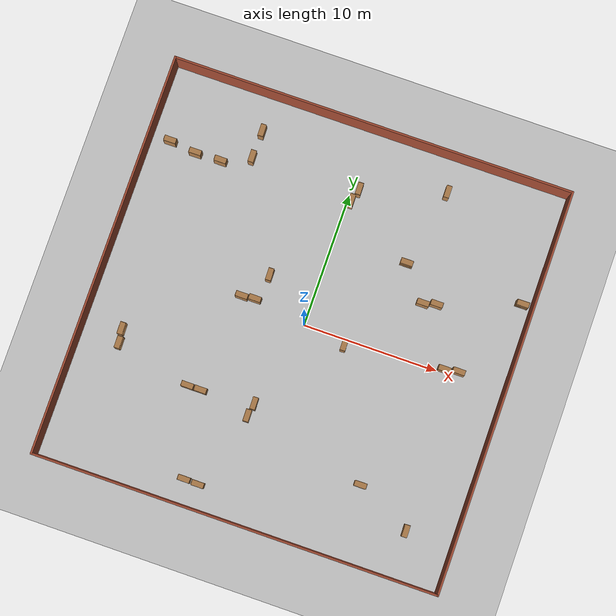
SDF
<sdf version="1.6">
 <world name="default">
  <light name="sun" type="directional">
   <pose>0 0 10 0 -0 0</pose>
   <diffuse>0.8 0.8 0.8 1</diffuse>
   <specular>0.2 0.2 0.2 1</specular>
   <attenuation>
    <range>1000</range>
    <constant>0.9</constant>
    <linear>0.01</linear>
    <quadratic>0.001</quadratic>
   </attenuation>
   <direction>-0.5 0.1 -0.9</direction>
  </light>
  <model name="ground_plane">
   <static>1</static>
   <link name="link">
    <collision name="collision">
     <geometry><plane><normal>0 0 1</normal><size>100 100</size></plane></geometry>
     <surface>
      <contact><collide_bitmask>65535</collide_bitmask></contact>
      <friction><ode><mu>100</mu><mu2>50</mu2></ode></friction>
     </surface>
    </collision>
    <visual name="visual">
     <cast_shadows>0</cast_shadows>
     <geometry><plane><normal>0 0 1</normal><size>100 100</size></plane></geometry>
     <material>
      <script><uri>file://media/materials/scripts/gazebo.material</uri><name>Gazebo/Grey</name></script>
     </material>
    </visual>
   </link>
  </model>
  <gravity>0 0 -9.8</gravity>
  <magnetic_field>6e-06 2.3e-05 -4.2e-05</magnetic_field>
  <atmosphere type="adiabatic"/>
  <physics name="default_physics" default="0" type="ode">
   <max_step_size>0.001</max_step_size>
   <real_time_factor>1</real_time_factor>
   <real_time_update_rate>1000</real_time_update_rate>
  </physics>
  <scene><ambient>0.4 0.4 0.4 1</ambient><background>0.7 0.7 0.7 1</background><shadows>1</shadows></scene>
  <spherical_coordinates>
   <surface_model>EARTH_WGS84</surface_model>
   <latitude_deg>0</latitude_deg>
   <longitude_deg>0</longitude_deg>
   <elevation>0</elevation>
   <heading_deg>0</heading_deg>
  </spherical_coordinates>
  <model name="30x30env"><static>0</static><pose>32.1206 3.39752 0 0 -0 0</pose></model>
  <model name="30x30_0">
   <link name="Wall_0">
    <collision name="Wall_0_Collision">
     <geometry><box><size>30.15 0.15 2.5</size></box></geometry>
     <pose>0 0 1.25 0 -0 0</pose>
    </collision>
    <visual name="Wall_0_Visual">
     <pose>0 0 1.25 0 -0 0</pose>
     <geometry><box><size>30.15 0.15 2.5</size></box></geometry>
     <material>
      <script><uri>file://media/materials/scripts/gazebo.material</uri><name>Gazebo/Bricks</name></script>
      <ambient>1 1 1 1</ambient>
     </material>
     <meta><layer>0</layer></meta>
    </visual>
    <pose>-15 0 0 0 -0 1.5708</pose>
   </link>
   <link name="Wall_1">
    <collision name="Wall_1_Collision">
     <geometry><box><size>30.15 0.15 2.5</size></box></geometry>
     <pose>0 0 1.25 0 -0 0</pose>
    </collision>
    <visual name="Wall_1_Visual">
     <pose>0 0 1.25 0 -0 0</pose>
     <geometry><box><size>30.15 0.15 2.5</size></box></geometry>
     <material>
      <script><uri>file://media/materials/scripts/gazebo.material</uri><name>Gazebo/Bricks</name></script>
      <ambient>1 1 1 1</ambient>
     </material>
     <meta><layer>0</layer></meta>
    </visual>
    <pose>0 15 0 0 -0 0</pose>
   </link>
   <link name="Wall_2">
    <collision name="Wall_2_Collision">
     <geometry><box><size>30.15 0.15 2.5</size></box></geometry>
     <pose>0 0 1.25 0 -0 0</pose>
    </collision>
    <visual name="Wall_2_Visual">
     <pose>0 0 1.25 0 -0 0</pose>
     <geometry><box><size>30.15 0.15 2.5</size></box></geometry>
     <material>
      <script><uri>file://media/materials/scripts/gazebo.material</uri><name>Gazebo/Bricks</name></script>
      <ambient>1 1 1 1</ambient>
     </material>
     <meta><layer>0</layer></meta>
    </visual>
    <pose>15 0 0 0 -0 -1.5708</pose>
   </link>
   <link name="Wall_3">
    <collision name="Wall_3_Collision">
     <geometry><box><size>30.15 0.15 2.5</size></box></geometry>
     <pose>0 0 1.25 0 -0 0</pose>
    </collision>
    <visual name="Wall_3_Visual">
     <pose>0 0 1.25 0 -0 0</pose>
     <geometry><box><size>30.15 0.15 2.5</size></box></geometry>
     <material>
      <script><uri>file://media/materials/scripts/gazebo.material</uri><name>Gazebo/Bricks</name></script>
      <ambient>1 1 1 1</ambient>
     </material>
     <meta><layer>0</layer></meta>
    </visual>
    <pose>0 -15 0 0 -0 3.14159</pose>
   </link>
   <static>1</static>
  </model>
  <audio><device>default</device></audio>
  <model name="bookshelf_clone_clone_clone_0_clone_0_clone_3_clone">
   <static>1</static>
   <link name="link">
    <inertial><mass>1</mass></inertial>
    <collision name="back">
     <pose>0 0.005 0.6 0 -0 0</pose>
     <geometry><box><size>0.9 0.01 1.2</size></box></geometry>
    </collision>
    <visual name="visual1">
     <pose>0 0.005 0.6 0 -0 0</pose>
     <geometry><box><size>0.9 0.01 1.2</size></box></geometry>
     <material>
      <script><uri>file://media/materials/scripts/gazebo.material</uri><name>Gazebo/Wood</name></script>
     </material>
    </visual>
    <collision name="left_side">
     <pose>0.45 -0.195 0.6 0 -0 0</pose>
     <geometry><box><size>0.02 0.4 1.2</size></box></geometry>
    </collision>
    <visual name="visual2">
     <pose>0.45 -0.195 0.6 0 -0 0</pose>
     <geometry><box><size>0.02 0.4 1.2</size></box></geometry>
     <material>
      <script><uri>file://media/materials/scripts/gazebo.material</uri><name>Gazebo/Wood</name></script>
     </material>
    </visual>
    <collision name="right_side">
     <pose>-0.45 -0.195 0.6 0 -0 0</pose>
     <geometry><box><size>0.02 0.4 1.2</size></box></geometry>
    </collision>
    <visual name="visual3">
     <pose>-0.45 -0.195 0.6 0 -0 0</pose>
     <geometry><box><size>0.02 0.4 1.2</size></box></geometry>
     <material>
      <script><uri>file://media/materials/scripts/gazebo.material</uri><name>Gazebo/Wood</name></script>
     </material>
    </visual>
    <collision name="bottom">
     <pose>0 -0.195 0.03 0 -0 0</pose>
     <geometry><box><size>0.88 0.4 0.06</size></box></geometry>
    </collision>
    <visual name="visual4">
     <pose>0 -0.195 0.03 0 -0 0</pose>
     <geometry><box><size>0.88 0.4 0.06</size></box></geometry>
     <material>
      <script><uri>file://media/materials/scripts/gazebo.material</uri><name>Gazebo/Wood</name></script>
     </material>
    </visual>
    <collision name="top">
     <pose>0 -0.195 1.19 0 -0 0</pose>
     <geometry><box><size>0.88 0.4 0.02</size></box></geometry>
    </collision>
    <visual name="visual5">
     <pose>0 -0.195 1.19 0 -0 0</pose>
     <geometry><box><size>0.88 0.4 0.02</size></box></geometry>
     <material>
      <script><uri>file://media/materials/scripts/gazebo.material</uri><name>Gazebo/Wood</name></script>
     </material>
    </visual>
    <collision name="low_shelf">
     <pose>0 -0.195 0.43 0 -0 0</pose>
     <geometry><box><size>0.88 0.4 0.02</size></box></geometry>
    </collision>
    <visual name="visual6">
     <pose>0 -0.195 0.43 0 -0 0</pose>
     <geometry><box><size>0.88 0.4 0.02</size></box></geometry>
     <material>
      <script><uri>file://media/materials/scripts/gazebo.material</uri><name>Gazebo/Wood</name></script>
     </material>
    </visual>
    <collision name="high_shelf">
     <pose>0 -0.195 0.8 0 -0 0</pose>
     <geometry><box><size>0.88 0.4 0.02</size></box></geometry>
    </collision>
    <visual name="visual7">
     <pose>0 -0.195 0.8 0 -0 0</pose>
     <geometry><box><size>0.88 0.4 0.02</size></box></geometry>
     <material>
      <script><uri>file://media/materials/scripts/gazebo.material</uri><name>Gazebo/Wood</name></script>
     </material>
    </visual>
   </link>
   <pose>14.2814 6.68434 0 0 -0 0</pose>
  </model>
  <model name="bookshelf_clone_clone_clone_0_clone_0_clone_3_clone_0_clone_0">
   <static>1</static>
   <link name="link">
    <inertial><mass>1</mass></inertial>
    <collision name="back">
     <pose>0 0.005 0.6 0 -0 0</pose>
     <geometry><box><size>0.9 0.01 1.2</size></box></geometry>
    </collision>
    <visual name="visual1">
     <pose>0 0.005 0.6 0 -0 0</pose>
     <geometry><box><size>0.9 0.01 1.2</size></box></geometry>
     <material>
      <script><uri>file://media/materials/scripts/gazebo.material</uri><name>Gazebo/Wood</name></script>
     </material>
    </visual>
    <collision name="left_side">
     <pose>0.45 -0.195 0.6 0 -0 0</pose>
     <geometry><box><size>0.02 0.4 1.2</size></box></geometry>
    </collision>
    <visual name="visual2">
     <pose>0.45 -0.195 0.6 0 -0 0</pose>
     <geometry><box><size>0.02 0.4 1.2</size></box></geometry>
     <material>
      <script><uri>file://media/materials/scripts/gazebo.material</uri><name>Gazebo/Wood</name></script>
     </material>
    </visual>
    <collision name="right_side">
     <pose>-0.45 -0.195 0.6 0 -0 0</pose>
     <geometry><box><size>0.02 0.4 1.2</size></box></geometry>
    </collision>
    <visual name="visual3">
     <pose>-0.45 -0.195 0.6 0 -0 0</pose>
     <geometry><box><size>0.02 0.4 1.2</size></box></geometry>
     <material>
      <script><uri>file://media/materials/scripts/gazebo.material</uri><name>Gazebo/Wood</name></script>
     </material>
    </visual>
    <collision name="bottom">
     <pose>0 -0.195 0.03 0 -0 0</pose>
     <geometry><box><size>0.88 0.4 0.06</size></box></geometry>
    </collision>
    <visual name="visual4">
     <pose>0 -0.195 0.03 0 -0 0</pose>
     <geometry><box><size>0.88 0.4 0.06</size></box></geometry>
     <material>
      <script><uri>file://media/materials/scripts/gazebo.material</uri><name>Gazebo/Wood</name></script>
     </material>
    </visual>
    <collision name="top">
     <pose>0 -0.195 1.19 0 -0 0</pose>
     <geometry><box><size>0.88 0.4 0.02</size></box></geometry>
    </collision>
    <visual name="visual5">
     <pose>0 -0.195 1.19 0 -0 0</pose>
     <geometry><box><size>0.88 0.4 0.02</size></box></geometry>
     <material>
      <script><uri>file://media/materials/scripts/gazebo.material</uri><name>Gazebo/Wood</name></script>
     </material>
    </visual>
    <collision name="low_shelf">
     <pose>0 -0.195 0.43 0 -0 0</pose>
     <geometry><box><size>0.88 0.4 0.02</size></box></geometry>
    </collision>
    <visual name="visual6">
     <pose>0 -0.195 0.43 0 -0 0</pose>
     <geometry><box><size>0.88 0.4 0.02</size></box></geometry>
     <material>
      <script><uri>file://media/materials/scripts/gazebo.material</uri><name>Gazebo/Wood</name></script>
     </material>
    </visual>
    <collision name="high_shelf">
     <pose>0 -0.195 0.8 0 -0 0</pose>
     <geometry><box><size>0.88 0.4 0.02</size></box></geometry>
    </collision>
    <visual name="visual7">
     <pose>0 -0.195 0.8 0 -0 0</pose>
     <geometry><box><size>0.88 0.4 0.02</size></box></geometry>
     <material>
      <script><uri>file://media/materials/scripts/gazebo.material</uri><name>Gazebo/Wood</name></script>
     </material>
    </visual>
   </link>
   <pose>6.42885 12.4053 0 0 -0 1.59147</pose>
  </model>
  <model name="bookshelf_clone_clone_clone_0_clone_0_clone_3_clone_clone_0">
   <static>1</static>
   <link name="link">
    <inertial><mass>1</mass></inertial>
    <collision name="back">
     <pose>0 0.005 0.6 0 -0 0</pose>
     <geometry><box><size>0.9 0.01 1.2</size></box></geometry>
    </collision>
    <visual name="visual1">
     <pose>0 0.005 0.6 0 -0 0</pose>
     <geometry><box><size>0.9 0.01 1.2</size></box></geometry>
     <material>
      <script><uri>file://media/materials/scripts/gazebo.material</uri><name>Gazebo/Wood</name></script>
     </material>
    </visual>
    <collision name="left_side">
     <pose>0.45 -0.195 0.6 0 -0 0</pose>
     <geometry><box><size>0.02 0.4 1.2</size></box></geometry>
    </collision>
    <visual name="visual2">
     <pose>0.45 -0.195 0.6 0 -0 0</pose>
     <geometry><box><size>0.02 0.4 1.2</size></box></geometry>
     <material>
      <script><uri>file://media/materials/scripts/gazebo.material</uri><name>Gazebo/Wood</name></script>
     </material>
    </visual>
    <collision name="right_side">
     <pose>-0.45 -0.195 0.6 0 -0 0</pose>
     <geometry><box><size>0.02 0.4 1.2</size></box></geometry>
    </collision>
    <visual name="visual3">
     <pose>-0.45 -0.195 0.6 0 -0 0</pose>
     <geometry><box><size>0.02 0.4 1.2</size></box></geometry>
     <material>
      <script><uri>file://media/materials/scripts/gazebo.material</uri><name>Gazebo/Wood</name></script>
     </material>
    </visual>
    <collision name="bottom">
     <pose>0 -0.195 0.03 0 -0 0</pose>
     <geometry><box><size>0.88 0.4 0.06</size></box></geometry>
    </collision>
    <visual name="visual4">
     <pose>0 -0.195 0.03 0 -0 0</pose>
     <geometry><box><size>0.88 0.4 0.06</size></box></geometry>
     <material>
      <script><uri>file://media/materials/scripts/gazebo.material</uri><name>Gazebo/Wood</name></script>
     </material>
    </visual>
    <collision name="top">
     <pose>0 -0.195 1.19 0 -0 0</pose>
     <geometry><box><size>0.88 0.4 0.02</size></box></geometry>
    </collision>
    <visual name="visual5">
     <pose>0 -0.195 1.19 0 -0 0</pose>
     <geometry><box><size>0.88 0.4 0.02</size></box></geometry>
     <material>
      <script><uri>file://media/materials/scripts/gazebo.material</uri><name>Gazebo/Wood</name></script>
     </material>
    </visual>
    <collision name="low_shelf">
     <pose>0 -0.195 0.43 0 -0 0</pose>
     <geometry><box><size>0.88 0.4 0.02</size></box></geometry>
    </collision>
    <visual name="visual6">
     <pose>0 -0.195 0.43 0 -0 0</pose>
     <geometry><box><size>0.88 0.4 0.02</size></box></geometry>
     <material>
      <script><uri>file://media/materials/scripts/gazebo.material</uri><name>Gazebo/Wood</name></script>
     </material>
    </visual>
    <collision name="high_shelf">
     <pose>0 -0.195 0.8 0 -0 0</pose>
     <geometry><box><size>0.88 0.4 0.02</size></box></geometry>
    </collision>
    <visual name="visual7">
     <pose>0 -0.195 0.8 0 -0 0</pose>
     <geometry><box><size>0.88 0.4 0.02</size></box></geometry>
     <material>
      <script><uri>file://media/materials/scripts/gazebo.material</uri><name>Gazebo/Wood</name></script>
     </material>
    </visual>
   </link>
   <pose>5.48865 6.80264 0 0 -0 0</pose>
  </model>
  <model name="bookshelf_clone_clone_clone_0_clone_0_clone_3_clone_clone_1_clone_clone">
   <static>1</static>
   <link name="link">
    <inertial><mass>1</mass></inertial>
    <collision name="back">
     <pose>0 0.005 0.6 0 -0 0</pose>
     <geometry><box><size>0.9 0.01 1.2</size></box></geometry>
    </collision>
    <visual name="visual1">
     <pose>0 0.005 0.6 0 -0 0</pose>
     <geometry><box><size>0.9 0.01 1.2</size></box></geometry>
     <material>
      <script><uri>file://media/materials/scripts/gazebo.material</uri><name>Gazebo/Wood</name></script>
     </material>
    </visual>
    <collision name="left_side">
     <pose>0.45 -0.195 0.6 0 -0 0</pose>
     <geometry><box><size>0.02 0.4 1.2</size></box></geometry>
    </collision>
    <visual name="visual2">
     <pose>0.45 -0.195 0.6 0 -0 0</pose>
     <geometry><box><size>0.02 0.4 1.2</size></box></geometry>
     <material>
      <script><uri>file://media/materials/scripts/gazebo.material</uri><name>Gazebo/Wood</name></script>
     </material>
    </visual>
    <collision name="right_side">
     <pose>-0.45 -0.195 0.6 0 -0 0</pose>
     <geometry><box><size>0.02 0.4 1.2</size></box></geometry>
    </collision>
    <visual name="visual3">
     <pose>-0.45 -0.195 0.6 0 -0 0</pose>
     <geometry><box><size>0.02 0.4 1.2</size></box></geometry>
     <material>
      <script><uri>file://media/materials/scripts/gazebo.material</uri><name>Gazebo/Wood</name></script>
     </material>
    </visual>
    <collision name="bottom">
     <pose>0 -0.195 0.03 0 -0 0</pose>
     <geometry><box><size>0.88 0.4 0.06</size></box></geometry>
    </collision>
    <visual name="visual4">
     <pose>0 -0.195 0.03 0 -0 0</pose>
     <geometry><box><size>0.88 0.4 0.06</size></box></geometry>
     <material>
      <script><uri>file://media/materials/scripts/gazebo.material</uri><name>Gazebo/Wood</name></script>
     </material>
    </visual>
    <collision name="top">
     <pose>0 -0.195 1.19 0 -0 0</pose>
     <geometry><box><size>0.88 0.4 0.02</size></box></geometry>
    </collision>
    <visual name="visual5">
     <pose>0 -0.195 1.19 0 -0 0</pose>
     <geometry><box><size>0.88 0.4 0.02</size></box></geometry>
     <material>
      <script><uri>file://media/materials/scripts/gazebo.material</uri><name>Gazebo/Wood</name></script>
     </material>
    </visual>
    <collision name="low_shelf">
     <pose>0 -0.195 0.43 0 -0 0</pose>
     <geometry><box><size>0.88 0.4 0.02</size></box></geometry>
    </collision>
    <visual name="visual6">
     <pose>0 -0.195 0.43 0 -0 0</pose>
     <geometry><box><size>0.88 0.4 0.02</size></box></geometry>
     <material>
      <script><uri>file://media/materials/scripts/gazebo.material</uri><name>Gazebo/Wood</name></script>
     </material>
    </visual>
    <collision name="high_shelf">
     <pose>0 -0.195 0.8 0 -0 0</pose>
     <geometry><box><size>0.88 0.4 0.02</size></box></geometry>
    </collision>
    <visual name="visual7">
     <pose>0 -0.195 0.8 0 -0 0</pose>
     <geometry><box><size>0.88 0.4 0.02</size></box></geometry>
     <material>
      <script><uri>file://media/materials/scripts/gazebo.material</uri><name>Gazebo/Wood</name></script>
     </material>
    </visual>
   </link>
   <pose>7.51774 4.03008 0 0 -0 3.1368</pose>
  </model>
  <model name="bookshelf_clone_clone_clone_0_clone_0_clone_3_clone_clone_1_clone_clone_clone">
   <static>1</static>
   <link name="link">
    <inertial><mass>1</mass></inertial>
    <collision name="back">
     <pose>0 0.005 0.6 0 -0 0</pose>
     <geometry><box><size>0.9 0.01 1.2</size></box></geometry>
    </collision>
    <visual name="visual1">
     <pose>0 0.005 0.6 0 -0 0</pose>
     <geometry><box><size>0.9 0.01 1.2</size></box></geometry>
     <material>
      <script><uri>file://media/materials/scripts/gazebo.material</uri><name>Gazebo/Wood</name></script>
     </material>
    </visual>
    <collision name="left_side">
     <pose>0.45 -0.195 0.6 0 -0 0</pose>
     <geometry><box><size>0.02 0.4 1.2</size></box></geometry>
    </collision>
    <visual name="visual2">
     <pose>0.45 -0.195 0.6 0 -0 0</pose>
     <geometry><box><size>0.02 0.4 1.2</size></box></geometry>
     <material>
      <script><uri>file://media/materials/scripts/gazebo.material</uri><name>Gazebo/Wood</name></script>
     </material>
    </visual>
    <collision name="right_side">
     <pose>-0.45 -0.195 0.6 0 -0 0</pose>
     <geometry><box><size>0.02 0.4 1.2</size></box></geometry>
    </collision>
    <visual name="visual3">
     <pose>-0.45 -0.195 0.6 0 -0 0</pose>
     <geometry><box><size>0.02 0.4 1.2</size></box></geometry>
     <material>
      <script><uri>file://media/materials/scripts/gazebo.material</uri><name>Gazebo/Wood</name></script>
     </material>
    </visual>
    <collision name="bottom">
     <pose>0 -0.195 0.03 0 -0 0</pose>
     <geometry><box><size>0.88 0.4 0.06</size></box></geometry>
    </collision>
    <visual name="visual4">
     <pose>0 -0.195 0.03 0 -0 0</pose>
     <geometry><box><size>0.88 0.4 0.06</size></box></geometry>
     <material>
      <script><uri>file://media/materials/scripts/gazebo.material</uri><name>Gazebo/Wood</name></script>
     </material>
    </visual>
    <collision name="top">
     <pose>0 -0.195 1.19 0 -0 0</pose>
     <geometry><box><size>0.88 0.4 0.02</size></box></geometry>
    </collision>
    <visual name="visual5">
     <pose>0 -0.195 1.19 0 -0 0</pose>
     <geometry><box><size>0.88 0.4 0.02</size></box></geometry>
     <material>
      <script><uri>file://media/materials/scripts/gazebo.material</uri><name>Gazebo/Wood</name></script>
     </material>
    </visual>
    <collision name="low_shelf">
     <pose>0 -0.195 0.43 0 -0 0</pose>
     <geometry><box><size>0.88 0.4 0.02</size></box></geometry>
    </collision>
    <visual name="visual6">
     <pose>0 -0.195 0.43 0 -0 0</pose>
     <geometry><box><size>0.88 0.4 0.02</size></box></geometry>
     <material>
      <script><uri>file://media/materials/scripts/gazebo.material</uri><name>Gazebo/Wood</name></script>
     </material>
    </visual>
    <collision name="high_shelf">
     <pose>0 -0.195 0.8 0 -0 0</pose>
     <geometry><box><size>0.88 0.4 0.02</size></box></geometry>
    </collision>
    <visual name="visual7">
     <pose>0 -0.195 0.8 0 -0 0</pose>
     <geometry><box><size>0.88 0.4 0.02</size></box></geometry>
     <material>
      <script><uri>file://media/materials/scripts/gazebo.material</uri><name>Gazebo/Wood</name></script>
     </material>
    </visual>
   </link>
   <pose>8.47007 4.27457 0 0 -0 3.1368</pose>
  </model>
  <model name="bookshelf_clone_clone_clone_0_clone_0_clone_3_clone_clone_1_clone_clone_clone_0">
   <static>1</static>
   <link name="link">
    <inertial><mass>1</mass></inertial>
    <collision name="back">
     <pose>0 0.005 0.6 0 -0 0</pose>
     <geometry><box><size>0.9 0.01 1.2</size></box></geometry>
    </collision>
    <visual name="visual1">
     <pose>0 0.005 0.6 0 -0 0</pose>
     <geometry><box><size>0.9 0.01 1.2</size></box></geometry>
     <material>
      <script><uri>file://media/materials/scripts/gazebo.material</uri><name>Gazebo/Wood</name></script>
     </material>
    </visual>
    <collision name="left_side">
     <pose>0.45 -0.195 0.6 0 -0 0</pose>
     <geometry><box><size>0.02 0.4 1.2</size></box></geometry>
    </collision>
    <visual name="visual2">
     <pose>0.45 -0.195 0.6 0 -0 0</pose>
     <geometry><box><size>0.02 0.4 1.2</size></box></geometry>
     <material>
      <script><uri>file://media/materials/scripts/gazebo.material</uri><name>Gazebo/Wood</name></script>
     </material>
    </visual>
    <collision name="right_side">
     <pose>-0.45 -0.195 0.6 0 -0 0</pose>
     <geometry><box><size>0.02 0.4 1.2</size></box></geometry>
    </collision>
    <visual name="visual3">
     <pose>-0.45 -0.195 0.6 0 -0 0</pose>
     <geometry><box><size>0.02 0.4 1.2</size></box></geometry>
     <material>
      <script><uri>file://media/materials/scripts/gazebo.material</uri><name>Gazebo/Wood</name></script>
     </material>
    </visual>
    <collision name="bottom">
     <pose>0 -0.195 0.03 0 -0 0</pose>
     <geometry><box><size>0.88 0.4 0.06</size></box></geometry>
    </collision>
    <visual name="visual4">
     <pose>0 -0.195 0.03 0 -0 0</pose>
     <geometry><box><size>0.88 0.4 0.06</size></box></geometry>
     <material>
      <script><uri>file://media/materials/scripts/gazebo.material</uri><name>Gazebo/Wood</name></script>
     </material>
    </visual>
    <collision name="top">
     <pose>0 -0.195 1.19 0 -0 0</pose>
     <geometry><box><size>0.88 0.4 0.02</size></box></geometry>
    </collision>
    <visual name="visual5">
     <pose>0 -0.195 1.19 0 -0 0</pose>
     <geometry><box><size>0.88 0.4 0.02</size></box></geometry>
     <material>
      <script><uri>file://media/materials/scripts/gazebo.material</uri><name>Gazebo/Wood</name></script>
     </material>
    </visual>
    <collision name="low_shelf">
     <pose>0 -0.195 0.43 0 -0 0</pose>
     <geometry><box><size>0.88 0.4 0.02</size></box></geometry>
    </collision>
    <visual name="visual6">
     <pose>0 -0.195 0.43 0 -0 0</pose>
     <geometry><box><size>0.88 0.4 0.02</size></box></geometry>
     <material>
      <script><uri>file://media/materials/scripts/gazebo.material</uri><name>Gazebo/Wood</name></script>
     </material>
    </visual>
    <collision name="high_shelf">
     <pose>0 -0.195 0.8 0 -0 0</pose>
     <geometry><box><size>0.88 0.4 0.02</size></box></geometry>
    </collision>
    <visual name="visual7">
     <pose>0 -0.195 0.8 0 -0 0</pose>
     <geometry><box><size>0.88 0.4 0.02</size></box></geometry>
     <material>
      <script><uri>file://media/materials/scripts/gazebo.material</uri><name>Gazebo/Wood</name></script>
     </material>
    </visual>
   </link>
   <pose>10.4865 0.040124 0 0 -0 3.1368</pose>
  </model>
  <model name="bookshelf_clone_clone_clone_0_clone_0_clone_3_clone_clone_1_clone_clone_clone_1">
   <static>1</static>
   <link name="link">
    <inertial><mass>1</mass></inertial>
    <collision name="back">
     <pose>0 0.005 0.6 0 -0 0</pose>
     <geometry><box><size>0.9 0.01 1.2</size></box></geometry>
    </collision>
    <visual name="visual1">
     <pose>0 0.005 0.6 0 -0 0</pose>
     <geometry><box><size>0.9 0.01 1.2</size></box></geometry>
     <material>
      <script><uri>file://media/materials/scripts/gazebo.material</uri><name>Gazebo/Wood</name></script>
     </material>
    </visual>
    <collision name="left_side">
     <pose>0.45 -0.195 0.6 0 -0 0</pose>
     <geometry><box><size>0.02 0.4 1.2</size></box></geometry>
    </collision>
    <visual name="visual2">
     <pose>0.45 -0.195 0.6 0 -0 0</pose>
     <geometry><box><size>0.02 0.4 1.2</size></box></geometry>
     <material>
      <script><uri>file://media/materials/scripts/gazebo.material</uri><name>Gazebo/Wood</name></script>
     </material>
    </visual>
    <collision name="right_side">
     <pose>-0.45 -0.195 0.6 0 -0 0</pose>
     <geometry><box><size>0.02 0.4 1.2</size></box></geometry>
    </collision>
    <visual name="visual3">
     <pose>-0.45 -0.195 0.6 0 -0 0</pose>
     <geometry><box><size>0.02 0.4 1.2</size></box></geometry>
     <material>
      <script><uri>file://media/materials/scripts/gazebo.material</uri><name>Gazebo/Wood</name></script>
     </material>
    </visual>
    <collision name="bottom">
     <pose>0 -0.195 0.03 0 -0 0</pose>
     <geometry><box><size>0.88 0.4 0.06</size></box></geometry>
    </collision>
    <visual name="visual4">
     <pose>0 -0.195 0.03 0 -0 0</pose>
     <geometry><box><size>0.88 0.4 0.06</size></box></geometry>
     <material>
      <script><uri>file://media/materials/scripts/gazebo.material</uri><name>Gazebo/Wood</name></script>
     </material>
    </visual>
    <collision name="top">
     <pose>0 -0.195 1.19 0 -0 0</pose>
     <geometry><box><size>0.88 0.4 0.02</size></box></geometry>
    </collision>
    <visual name="visual5">
     <pose>0 -0.195 1.19 0 -0 0</pose>
     <geometry><box><size>0.88 0.4 0.02</size></box></geometry>
     <material>
      <script><uri>file://media/materials/scripts/gazebo.material</uri><name>Gazebo/Wood</name></script>
     </material>
    </visual>
    <collision name="low_shelf">
     <pose>0 -0.195 0.43 0 -0 0</pose>
     <geometry><box><size>0.88 0.4 0.02</size></box></geometry>
    </collision>
    <visual name="visual6">
     <pose>0 -0.195 0.43 0 -0 0</pose>
     <geometry><box><size>0.88 0.4 0.02</size></box></geometry>
     <material>
      <script><uri>file://media/materials/scripts/gazebo.material</uri><name>Gazebo/Wood</name></script>
     </material>
    </visual>
    <collision name="high_shelf">
     <pose>0 -0.195 0.8 0 -0 0</pose>
     <geometry><box><size>0.88 0.4 0.02</size></box></geometry>
    </collision>
    <visual name="visual7">
     <pose>0 -0.195 0.8 0 -0 0</pose>
     <geometry><box><size>0.88 0.4 0.02</size></box></geometry>
     <material>
      <script><uri>file://media/materials/scripts/gazebo.material</uri><name>Gazebo/Wood</name></script>
     </material>
    </visual>
   </link>
   <pose>11.5073 0.210464 0 0 -0 3.1368</pose>
  </model>
  <model name="bookshelf_clone_clone_clone_0_clone_0_clone_3_clone_0_clone_clone_clone_clone_0">
   <static>1</static>
   <link name="link">
    <inertial><mass>1</mass></inertial>
    <collision name="back">
     <pose>0 0.005 0.6 0 -0 0</pose>
     <geometry><box><size>0.9 0.01 1.2</size></box></geometry>
    </collision>
    <visual name="visual1">
     <pose>0 0.005 0.6 0 -0 0</pose>
     <geometry><box><size>0.9 0.01 1.2</size></box></geometry>
     <material>
      <script><uri>file://media/materials/scripts/gazebo.material</uri><name>Gazebo/Wood</name></script>
     </material>
    </visual>
    <collision name="left_side">
     <pose>0.45 -0.195 0.6 0 -0 0</pose>
     <geometry><box><size>0.02 0.4 1.2</size></box></geometry>
    </collision>
    <visual name="visual2">
     <pose>0.45 -0.195 0.6 0 -0 0</pose>
     <geometry><box><size>0.02 0.4 1.2</size></box></geometry>
     <material>
      <script><uri>file://media/materials/scripts/gazebo.material</uri><name>Gazebo/Wood</name></script>
     </material>
    </visual>
    <collision name="right_side">
     <pose>-0.45 -0.195 0.6 0 -0 0</pose>
     <geometry><box><size>0.02 0.4 1.2</size></box></geometry>
    </collision>
    <visual name="visual3">
     <pose>-0.45 -0.195 0.6 0 -0 0</pose>
     <geometry><box><size>0.02 0.4 1.2</size></box></geometry>
     <material>
      <script><uri>file://media/materials/scripts/gazebo.material</uri><name>Gazebo/Wood</name></script>
     </material>
    </visual>
    <collision name="bottom">
     <pose>0 -0.195 0.03 0 -0 0</pose>
     <geometry><box><size>0.88 0.4 0.06</size></box></geometry>
    </collision>
    <visual name="visual4">
     <pose>0 -0.195 0.03 0 -0 0</pose>
     <geometry><box><size>0.88 0.4 0.06</size></box></geometry>
     <material>
      <script><uri>file://media/materials/scripts/gazebo.material</uri><name>Gazebo/Wood</name></script>
     </material>
    </visual>
    <collision name="top">
     <pose>0 -0.195 1.19 0 -0 0</pose>
     <geometry><box><size>0.88 0.4 0.02</size></box></geometry>
    </collision>
    <visual name="visual5">
     <pose>0 -0.195 1.19 0 -0 0</pose>
     <geometry><box><size>0.88 0.4 0.02</size></box></geometry>
     <material>
      <script><uri>file://media/materials/scripts/gazebo.material</uri><name>Gazebo/Wood</name></script>
     </material>
    </visual>
    <collision name="low_shelf">
     <pose>0 -0.195 0.43 0 -0 0</pose>
     <geometry><box><size>0.88 0.4 0.02</size></box></geometry>
    </collision>
    <visual name="visual6">
     <pose>0 -0.195 0.43 0 -0 0</pose>
     <geometry><box><size>0.88 0.4 0.02</size></box></geometry>
     <material>
      <script><uri>file://media/materials/scripts/gazebo.material</uri><name>Gazebo/Wood</name></script>
     </material>
    </visual>
    <collision name="high_shelf">
     <pose>0 -0.195 0.8 0 -0 0</pose>
     <geometry><box><size>0.88 0.4 0.02</size></box></geometry>
    </collision>
    <visual name="visual7">
     <pose>0 -0.195 0.8 0 -0 0</pose>
     <geometry><box><size>0.88 0.4 0.02</size></box></geometry>
     <material>
      <script><uri>file://media/materials/scripts/gazebo.material</uri><name>Gazebo/Wood</name></script>
     </material>
    </visual>
   </link>
   <pose>11.3706 -11.5079 0 0 -0 1.59147</pose>
  </model>
  <model name="bookshelf_clone_clone_clone_0_clone_0_clone_3_clone_clone_2">
   <static>1</static>
   <link name="link">
    <inertial><mass>1</mass></inertial>
    <collision name="back">
     <pose>0 0.005 0.6 0 -0 0</pose>
     <geometry><box><size>0.9 0.01 1.2</size></box></geometry>
    </collision>
    <visual name="visual1">
     <pose>0 0.005 0.6 0 -0 0</pose>
     <geometry><box><size>0.9 0.01 1.2</size></box></geometry>
     <material>
      <script><uri>file://media/materials/scripts/gazebo.material</uri><name>Gazebo/Wood</name></script>
     </material>
    </visual>
    <collision name="left_side">
     <pose>0.45 -0.195 0.6 0 -0 0</pose>
     <geometry><box><size>0.02 0.4 1.2</size></box></geometry>
    </collision>
    <visual name="visual2">
     <pose>0.45 -0.195 0.6 0 -0 0</pose>
     <geometry><box><size>0.02 0.4 1.2</size></box></geometry>
     <material>
      <script><uri>file://media/materials/scripts/gazebo.material</uri><name>Gazebo/Wood</name></script>
     </material>
    </visual>
    <collision name="right_side">
     <pose>-0.45 -0.195 0.6 0 -0 0</pose>
     <geometry><box><size>0.02 0.4 1.2</size></box></geometry>
    </collision>
    <visual name="visual3">
     <pose>-0.45 -0.195 0.6 0 -0 0</pose>
     <geometry><box><size>0.02 0.4 1.2</size></box></geometry>
     <material>
      <script><uri>file://media/materials/scripts/gazebo.material</uri><name>Gazebo/Wood</name></script>
     </material>
    </visual>
    <collision name="bottom">
     <pose>0 -0.195 0.03 0 -0 0</pose>
     <geometry><box><size>0.88 0.4 0.06</size></box></geometry>
    </collision>
    <visual name="visual4">
     <pose>0 -0.195 0.03 0 -0 0</pose>
     <geometry><box><size>0.88 0.4 0.06</size></box></geometry>
     <material>
      <script><uri>file://media/materials/scripts/gazebo.material</uri><name>Gazebo/Wood</name></script>
     </material>
    </visual>
    <collision name="top">
     <pose>0 -0.195 1.19 0 -0 0</pose>
     <geometry><box><size>0.88 0.4 0.02</size></box></geometry>
    </collision>
    <visual name="visual5">
     <pose>0 -0.195 1.19 0 -0 0</pose>
     <geometry><box><size>0.88 0.4 0.02</size></box></geometry>
     <material>
      <script><uri>file://media/materials/scripts/gazebo.material</uri><name>Gazebo/Wood</name></script>
     </material>
    </visual>
    <collision name="low_shelf">
     <pose>0 -0.195 0.43 0 -0 0</pose>
     <geometry><box><size>0.88 0.4 0.02</size></box></geometry>
    </collision>
    <visual name="visual6">
     <pose>0 -0.195 0.43 0 -0 0</pose>
     <geometry><box><size>0.88 0.4 0.02</size></box></geometry>
     <material>
      <script><uri>file://media/materials/scripts/gazebo.material</uri><name>Gazebo/Wood</name></script>
     </material>
    </visual>
    <collision name="high_shelf">
     <pose>0 -0.195 0.8 0 -0 0</pose>
     <geometry><box><size>0.88 0.4 0.02</size></box></geometry>
    </collision>
    <visual name="visual7">
     <pose>0 -0.195 0.8 0 -0 0</pose>
     <geometry><box><size>0.88 0.4 0.02</size></box></geometry>
     <material>
      <script><uri>file://media/materials/scripts/gazebo.material</uri><name>Gazebo/Wood</name></script>
     </material>
    </visual>
   </link>
   <pose>7.48796 -9.28472 0 0 -0 0</pose>
  </model>
  <model name="bookshelf_clone_clone_clone_0_clone_0_clone_3_clone_0_clone_clone_clone_clone_clone_clone">
   <static>1</static>
   <link name="link">
    <inertial><mass>1</mass></inertial>
    <collision name="back">
     <pose>0 0.005 0.6 0 -0 0</pose>
     <geometry><box><size>0.9 0.01 1.2</size></box></geometry>
    </collision>
    <visual name="visual1">
     <pose>0 0.005 0.6 0 -0 0</pose>
     <geometry><box><size>0.9 0.01 1.2</size></box></geometry>
     <material>
      <script><uri>file://media/materials/scripts/gazebo.material</uri><name>Gazebo/Wood</name></script>
     </material>
    </visual>
    <collision name="left_side">
     <pose>0.45 -0.195 0.6 0 -0 0</pose>
     <geometry><box><size>0.02 0.4 1.2</size></box></geometry>
    </collision>
    <visual name="visual2">
     <pose>0.45 -0.195 0.6 0 -0 0</pose>
     <geometry><box><size>0.02 0.4 1.2</size></box></geometry>
     <material>
      <script><uri>file://media/materials/scripts/gazebo.material</uri><name>Gazebo/Wood</name></script>
     </material>
    </visual>
    <collision name="right_side">
     <pose>-0.45 -0.195 0.6 0 -0 0</pose>
     <geometry><box><size>0.02 0.4 1.2</size></box></geometry>
    </collision>
    <visual name="visual3">
     <pose>-0.45 -0.195 0.6 0 -0 0</pose>
     <geometry><box><size>0.02 0.4 1.2</size></box></geometry>
     <material>
      <script><uri>file://media/materials/scripts/gazebo.material</uri><name>Gazebo/Wood</name></script>
     </material>
    </visual>
    <collision name="bottom">
     <pose>0 -0.195 0.03 0 -0 0</pose>
     <geometry><box><size>0.88 0.4 0.06</size></box></geometry>
    </collision>
    <visual name="visual4">
     <pose>0 -0.195 0.03 0 -0 0</pose>
     <geometry><box><size>0.88 0.4 0.06</size></box></geometry>
     <material>
      <script><uri>file://media/materials/scripts/gazebo.material</uri><name>Gazebo/Wood</name></script>
     </material>
    </visual>
    <collision name="top">
     <pose>0 -0.195 1.19 0 -0 0</pose>
     <geometry><box><size>0.88 0.4 0.02</size></box></geometry>
    </collision>
    <visual name="visual5">
     <pose>0 -0.195 1.19 0 -0 0</pose>
     <geometry><box><size>0.88 0.4 0.02</size></box></geometry>
     <material>
      <script><uri>file://media/materials/scripts/gazebo.material</uri><name>Gazebo/Wood</name></script>
     </material>
    </visual>
    <collision name="low_shelf">
     <pose>0 -0.195 0.43 0 -0 0</pose>
     <geometry><box><size>0.88 0.4 0.02</size></box></geometry>
    </collision>
    <visual name="visual6">
     <pose>0 -0.195 0.43 0 -0 0</pose>
     <geometry><box><size>0.88 0.4 0.02</size></box></geometry>
     <material>
      <script><uri>file://media/materials/scripts/gazebo.material</uri><name>Gazebo/Wood</name></script>
     </material>
    </visual>
    <collision name="high_shelf">
     <pose>0 -0.195 0.8 0 -0 0</pose>
     <geometry><box><size>0.88 0.4 0.02</size></box></geometry>
    </collision>
    <visual name="visual7">
     <pose>0 -0.195 0.8 0 -0 0</pose>
     <geometry><box><size>0.88 0.4 0.02</size></box></geometry>
     <material>
      <script><uri>file://media/materials/scripts/gazebo.material</uri><name>Gazebo/Wood</name></script>
     </material>
    </visual>
   </link>
   <pose>3.36575 -0.464775 0 0 0 -1.55111</pose>
  </model>
  <model name="bookshelf_clone_clone_clone_0_clone_0_clone_3_clone_0_clone_clone_clone_clone_clone_clone_clone_clone">
   <static>1</static>
   <link name="link">
    <inertial><mass>1</mass></inertial>
    <collision name="back">
     <pose>0 0.005 0.6 0 -0 0</pose>
     <geometry><box><size>0.9 0.01 1.2</size></box></geometry>
    </collision>
    <visual name="visual1">
     <pose>0 0.005 0.6 0 -0 0</pose>
     <geometry><box><size>0.9 0.01 1.2</size></box></geometry>
     <material>
      <script><uri>file://media/materials/scripts/gazebo.material</uri><name>Gazebo/Wood</name></script>
     </material>
    </visual>
    <collision name="left_side">
     <pose>0.45 -0.195 0.6 0 -0 0</pose>
     <geometry><box><size>0.02 0.4 1.2</size></box></geometry>
    </collision>
    <visual name="visual2">
     <pose>0.45 -0.195 0.6 0 -0 0</pose>
     <geometry><box><size>0.02 0.4 1.2</size></box></geometry>
     <material>
      <script><uri>file://media/materials/scripts/gazebo.material</uri><name>Gazebo/Wood</name></script>
     </material>
    </visual>
    <collision name="right_side">
     <pose>-0.45 -0.195 0.6 0 -0 0</pose>
     <geometry><box><size>0.02 0.4 1.2</size></box></geometry>
    </collision>
    <visual name="visual3">
     <pose>-0.45 -0.195 0.6 0 -0 0</pose>
     <geometry><box><size>0.02 0.4 1.2</size></box></geometry>
     <material>
      <script><uri>file://media/materials/scripts/gazebo.material</uri><name>Gazebo/Wood</name></script>
     </material>
    </visual>
    <collision name="bottom">
     <pose>0 -0.195 0.03 0 -0 0</pose>
     <geometry><box><size>0.88 0.4 0.06</size></box></geometry>
    </collision>
    <visual name="visual4">
     <pose>0 -0.195 0.03 0 -0 0</pose>
     <geometry><box><size>0.88 0.4 0.06</size></box></geometry>
     <material>
      <script><uri>file://media/materials/scripts/gazebo.material</uri><name>Gazebo/Wood</name></script>
     </material>
    </visual>
    <collision name="top">
     <pose>0 -0.195 1.19 0 -0 0</pose>
     <geometry><box><size>0.88 0.4 0.02</size></box></geometry>
    </collision>
    <visual name="visual5">
     <pose>0 -0.195 1.19 0 -0 0</pose>
     <geometry><box><size>0.88 0.4 0.02</size></box></geometry>
     <material>
      <script><uri>file://media/materials/scripts/gazebo.material</uri><name>Gazebo/Wood</name></script>
     </material>
    </visual>
    <collision name="low_shelf">
     <pose>0 -0.195 0.43 0 -0 0</pose>
     <geometry><box><size>0.88 0.4 0.02</size></box></geometry>
    </collision>
    <visual name="visual6">
     <pose>0 -0.195 0.43 0 -0 0</pose>
     <geometry><box><size>0.88 0.4 0.02</size></box></geometry>
     <material>
      <script><uri>file://media/materials/scripts/gazebo.material</uri><name>Gazebo/Wood</name></script>
     </material>
    </visual>
    <collision name="high_shelf">
     <pose>0 -0.195 0.8 0 -0 0</pose>
     <geometry><box><size>0.88 0.4 0.02</size></box></geometry>
    </collision>
    <visual name="visual7">
     <pose>0 -0.195 0.8 0 -0 0</pose>
     <geometry><box><size>0.88 0.4 0.02</size></box></geometry>
     <material>
      <script><uri>file://media/materials/scripts/gazebo.material</uri><name>Gazebo/Wood</name></script>
     </material>
    </visual>
   </link>
   <pose>0.461987 9.57614 0 0 0 -1.55111</pose>
  </model>
  <model name="bookshelf_clone_clone_clone_0_clone_0_clone_3_clone_0_clone_clone_clone_clone_clone_clone_clone_clone_0">
   <static>1</static>
   <link name="link">
    <inertial><mass>1</mass></inertial>
    <collision name="back">
     <pose>0 0.005 0.6 0 -0 0</pose>
     <geometry><box><size>0.9 0.01 1.2</size></box></geometry>
    </collision>
    <visual name="visual1">
     <pose>0 0.005 0.6 0 -0 0</pose>
     <geometry><box><size>0.9 0.01 1.2</size></box></geometry>
     <material>
      <script><uri>file://media/materials/scripts/gazebo.material</uri><name>Gazebo/Wood</name></script>
     </material>
    </visual>
    <collision name="left_side">
     <pose>0.45 -0.195 0.6 0 -0 0</pose>
     <geometry><box><size>0.02 0.4 1.2</size></box></geometry>
    </collision>
    <visual name="visual2">
     <pose>0.45 -0.195 0.6 0 -0 0</pose>
     <geometry><box><size>0.02 0.4 1.2</size></box></geometry>
     <material>
      <script><uri>file://media/materials/scripts/gazebo.material</uri><name>Gazebo/Wood</name></script>
     </material>
    </visual>
    <collision name="right_side">
     <pose>-0.45 -0.195 0.6 0 -0 0</pose>
     <geometry><box><size>0.02 0.4 1.2</size></box></geometry>
    </collision>
    <visual name="visual3">
     <pose>-0.45 -0.195 0.6 0 -0 0</pose>
     <geometry><box><size>0.02 0.4 1.2</size></box></geometry>
     <material>
      <script><uri>file://media/materials/scripts/gazebo.material</uri><name>Gazebo/Wood</name></script>
     </material>
    </visual>
    <collision name="bottom">
     <pose>0 -0.195 0.03 0 -0 0</pose>
     <geometry><box><size>0.88 0.4 0.06</size></box></geometry>
    </collision>
    <visual name="visual4">
     <pose>0 -0.195 0.03 0 -0 0</pose>
     <geometry><box><size>0.88 0.4 0.06</size></box></geometry>
     <material>
      <script><uri>file://media/materials/scripts/gazebo.material</uri><name>Gazebo/Wood</name></script>
     </material>
    </visual>
    <collision name="top">
     <pose>0 -0.195 1.19 0 -0 0</pose>
     <geometry><box><size>0.88 0.4 0.02</size></box></geometry>
    </collision>
    <visual name="visual5">
     <pose>0 -0.195 1.19 0 -0 0</pose>
     <geometry><box><size>0.88 0.4 0.02</size></box></geometry>
     <material>
      <script><uri>file://media/materials/scripts/gazebo.material</uri><name>Gazebo/Wood</name></script>
     </material>
    </visual>
    <collision name="low_shelf">
     <pose>0 -0.195 0.43 0 -0 0</pose>
     <geometry><box><size>0.88 0.4 0.02</size></box></geometry>
    </collision>
    <visual name="visual6">
     <pose>0 -0.195 0.43 0 -0 0</pose>
     <geometry><box><size>0.88 0.4 0.02</size></box></geometry>
     <material>
      <script><uri>file://media/materials/scripts/gazebo.material</uri><name>Gazebo/Wood</name></script>
     </material>
    </visual>
    <collision name="high_shelf">
     <pose>0 -0.195 0.8 0 -0 0</pose>
     <geometry><box><size>0.88 0.4 0.02</size></box></geometry>
    </collision>
    <visual name="visual7">
     <pose>0 -0.195 0.8 0 -0 0</pose>
     <geometry><box><size>0.88 0.4 0.02</size></box></geometry>
     <material>
      <script><uri>file://media/materials/scripts/gazebo.material</uri><name>Gazebo/Wood</name></script>
     </material>
    </visual>
   </link>
   <pose>0.730305 10.5409 0 0 0 -1.55111</pose>
  </model>
  <model name="bookshelf_clone_clone_clone_0_clone_0_clone_3_clone_0_clone_clone_clone_clone_0_clone_clone">
   <static>1</static>
   <link name="link">
    <inertial><mass>1</mass></inertial>
    <collision name="back">
     <pose>0 0.005 0.6 0 -0 0</pose>
     <geometry><box><size>0.9 0.01 1.2</size></box></geometry>
    </collision>
    <visual name="visual1">
     <pose>0 0.005 0.6 0 -0 0</pose>
     <geometry><box><size>0.9 0.01 1.2</size></box></geometry>
     <material>
      <script><uri>file://media/materials/scripts/gazebo.material</uri><name>Gazebo/Wood</name></script>
     </material>
    </visual>
    <collision name="left_side">
     <pose>0.45 -0.195 0.6 0 -0 0</pose>
     <geometry><box><size>0.02 0.4 1.2</size></box></geometry>
    </collision>
    <visual name="visual2">
     <pose>0.45 -0.195 0.6 0 -0 0</pose>
     <geometry><box><size>0.02 0.4 1.2</size></box></geometry>
     <material>
      <script><uri>file://media/materials/scripts/gazebo.material</uri><name>Gazebo/Wood</name></script>
     </material>
    </visual>
    <collision name="right_side">
     <pose>-0.45 -0.195 0.6 0 -0 0</pose>
     <geometry><box><size>0.02 0.4 1.2</size></box></geometry>
    </collision>
    <visual name="visual3">
     <pose>-0.45 -0.195 0.6 0 -0 0</pose>
     <geometry><box><size>0.02 0.4 1.2</size></box></geometry>
     <material>
      <script><uri>file://media/materials/scripts/gazebo.material</uri><name>Gazebo/Wood</name></script>
     </material>
    </visual>
    <collision name="bottom">
     <pose>0 -0.195 0.03 0 -0 0</pose>
     <geometry><box><size>0.88 0.4 0.06</size></box></geometry>
    </collision>
    <visual name="visual4">
     <pose>0 -0.195 0.03 0 -0 0</pose>
     <geometry><box><size>0.88 0.4 0.06</size></box></geometry>
     <material>
      <script><uri>file://media/materials/scripts/gazebo.material</uri><name>Gazebo/Wood</name></script>
     </material>
    </visual>
    <collision name="top">
     <pose>0 -0.195 1.19 0 -0 0</pose>
     <geometry><box><size>0.88 0.4 0.02</size></box></geometry>
    </collision>
    <visual name="visual5">
     <pose>0 -0.195 1.19 0 -0 0</pose>
     <geometry><box><size>0.88 0.4 0.02</size></box></geometry>
     <material>
      <script><uri>file://media/materials/scripts/gazebo.material</uri><name>Gazebo/Wood</name></script>
     </material>
    </visual>
    <collision name="low_shelf">
     <pose>0 -0.195 0.43 0 -0 0</pose>
     <geometry><box><size>0.88 0.4 0.02</size></box></geometry>
    </collision>
    <visual name="visual6">
     <pose>0 -0.195 0.43 0 -0 0</pose>
     <geometry><box><size>0.88 0.4 0.02</size></box></geometry>
     <material>
      <script><uri>file://media/materials/scripts/gazebo.material</uri><name>Gazebo/Wood</name></script>
     </material>
    </visual>
    <collision name="high_shelf">
     <pose>0 -0.195 0.8 0 -0 0</pose>
     <geometry><box><size>0.88 0.4 0.02</size></box></geometry>
    </collision>
    <visual name="visual7">
     <pose>0 -0.195 0.8 0 -0 0</pose>
     <geometry><box><size>0.88 0.4 0.02</size></box></geometry>
     <material>
      <script><uri>file://media/materials/scripts/gazebo.material</uri><name>Gazebo/Wood</name></script>
     </material>
    </visual>
   </link>
   <pose>-3.7014 2.55568 0 0 -0 1.59147</pose>
  </model>
  <model name="bookshelf_clone_clone_clone_0_clone_0_clone_3_clone_clone_1_clone_clone_clone_clone">
   <static>1</static>
   <link name="link">
    <inertial><mass>1</mass></inertial>
    <collision name="back">
     <pose>0 0.005 0.6 0 -0 0</pose>
     <geometry><box><size>0.9 0.01 1.2</size></box></geometry>
    </collision>
    <visual name="visual1">
     <pose>0 0.005 0.6 0 -0 0</pose>
     <geometry><box><size>0.9 0.01 1.2</size></box></geometry>
     <material>
      <script><uri>file://media/materials/scripts/gazebo.material</uri><name>Gazebo/Wood</name></script>
     </material>
    </visual>
    <collision name="left_side">
     <pose>0.45 -0.195 0.6 0 -0 0</pose>
     <geometry><box><size>0.02 0.4 1.2</size></box></geometry>
    </collision>
    <visual name="visual2">
     <pose>0.45 -0.195 0.6 0 -0 0</pose>
     <geometry><box><size>0.02 0.4 1.2</size></box></geometry>
     <material>
      <script><uri>file://media/materials/scripts/gazebo.material</uri><name>Gazebo/Wood</name></script>
     </material>
    </visual>
    <collision name="right_side">
     <pose>-0.45 -0.195 0.6 0 -0 0</pose>
     <geometry><box><size>0.02 0.4 1.2</size></box></geometry>
    </collision>
    <visual name="visual3">
     <pose>-0.45 -0.195 0.6 0 -0 0</pose>
     <geometry><box><size>0.02 0.4 1.2</size></box></geometry>
     <material>
      <script><uri>file://media/materials/scripts/gazebo.material</uri><name>Gazebo/Wood</name></script>
     </material>
    </visual>
    <collision name="bottom">
     <pose>0 -0.195 0.03 0 -0 0</pose>
     <geometry><box><size>0.88 0.4 0.06</size></box></geometry>
    </collision>
    <visual name="visual4">
     <pose>0 -0.195 0.03 0 -0 0</pose>
     <geometry><box><size>0.88 0.4 0.06</size></box></geometry>
     <material>
      <script><uri>file://media/materials/scripts/gazebo.material</uri><name>Gazebo/Wood</name></script>
     </material>
    </visual>
    <collision name="top">
     <pose>0 -0.195 1.19 0 -0 0</pose>
     <geometry><box><size>0.88 0.4 0.02</size></box></geometry>
    </collision>
    <visual name="visual5">
     <pose>0 -0.195 1.19 0 -0 0</pose>
     <geometry><box><size>0.88 0.4 0.02</size></box></geometry>
     <material>
      <script><uri>file://media/materials/scripts/gazebo.material</uri><name>Gazebo/Wood</name></script>
     </material>
    </visual>
    <collision name="low_shelf">
     <pose>0 -0.195 0.43 0 -0 0</pose>
     <geometry><box><size>0.88 0.4 0.02</size></box></geometry>
    </collision>
    <visual name="visual6">
     <pose>0 -0.195 0.43 0 -0 0</pose>
     <geometry><box><size>0.88 0.4 0.02</size></box></geometry>
     <material>
      <script><uri>file://media/materials/scripts/gazebo.material</uri><name>Gazebo/Wood</name></script>
     </material>
    </visual>
    <collision name="high_shelf">
     <pose>0 -0.195 0.8 0 -0 0</pose>
     <geometry><box><size>0.88 0.4 0.02</size></box></geometry>
    </collision>
    <visual name="visual7">
     <pose>0 -0.195 0.8 0 -0 0</pose>
     <geometry><box><size>0.88 0.4 0.02</size></box></geometry>
     <material>
      <script><uri>file://media/materials/scripts/gazebo.material</uri><name>Gazebo/Wood</name></script>
     </material>
    </visual>
   </link>
   <pose>-3.93703 0.396484 0 0 -0 3.1368</pose>
  </model>
  <model name="bookshelf_clone_clone_clone_0_clone_0_clone_3_clone_clone_1_clone_clone_clone_clone_0">
   <static>1</static>
   <link name="link">
    <inertial><mass>1</mass></inertial>
    <collision name="back">
     <pose>0 0.005 0.6 0 -0 0</pose>
     <geometry><box><size>0.9 0.01 1.2</size></box></geometry>
    </collision>
    <visual name="visual1">
     <pose>0 0.005 0.6 0 -0 0</pose>
     <geometry><box><size>0.9 0.01 1.2</size></box></geometry>
     <material>
      <script><uri>file://media/materials/scripts/gazebo.material</uri><name>Gazebo/Wood</name></script>
     </material>
    </visual>
    <collision name="left_side">
     <pose>0.45 -0.195 0.6 0 -0 0</pose>
     <geometry><box><size>0.02 0.4 1.2</size></box></geometry>
    </collision>
    <visual name="visual2">
     <pose>0.45 -0.195 0.6 0 -0 0</pose>
     <geometry><box><size>0.02 0.4 1.2</size></box></geometry>
     <material>
      <script><uri>file://media/materials/scripts/gazebo.material</uri><name>Gazebo/Wood</name></script>
     </material>
    </visual>
    <collision name="right_side">
     <pose>-0.45 -0.195 0.6 0 -0 0</pose>
     <geometry><box><size>0.02 0.4 1.2</size></box></geometry>
    </collision>
    <visual name="visual3">
     <pose>-0.45 -0.195 0.6 0 -0 0</pose>
     <geometry><box><size>0.02 0.4 1.2</size></box></geometry>
     <material>
      <script><uri>file://media/materials/scripts/gazebo.material</uri><name>Gazebo/Wood</name></script>
     </material>
    </visual>
    <collision name="bottom">
     <pose>0 -0.195 0.03 0 -0 0</pose>
     <geometry><box><size>0.88 0.4 0.06</size></box></geometry>
    </collision>
    <visual name="visual4">
     <pose>0 -0.195 0.03 0 -0 0</pose>
     <geometry><box><size>0.88 0.4 0.06</size></box></geometry>
     <material>
      <script><uri>file://media/materials/scripts/gazebo.material</uri><name>Gazebo/Wood</name></script>
     </material>
    </visual>
    <collision name="top">
     <pose>0 -0.195 1.19 0 -0 0</pose>
     <geometry><box><size>0.88 0.4 0.02</size></box></geometry>
    </collision>
    <visual name="visual5">
     <pose>0 -0.195 1.19 0 -0 0</pose>
     <geometry><box><size>0.88 0.4 0.02</size></box></geometry>
     <material>
      <script><uri>file://media/materials/scripts/gazebo.material</uri><name>Gazebo/Wood</name></script>
     </material>
    </visual>
    <collision name="low_shelf">
     <pose>0 -0.195 0.43 0 -0 0</pose>
     <geometry><box><size>0.88 0.4 0.02</size></box></geometry>
    </collision>
    <visual name="visual6">
     <pose>0 -0.195 0.43 0 -0 0</pose>
     <geometry><box><size>0.88 0.4 0.02</size></box></geometry>
     <material>
      <script><uri>file://media/materials/scripts/gazebo.material</uri><name>Gazebo/Wood</name></script>
     </material>
    </visual>
    <collision name="high_shelf">
     <pose>0 -0.195 0.8 0 -0 0</pose>
     <geometry><box><size>0.88 0.4 0.02</size></box></geometry>
    </collision>
    <visual name="visual7">
     <pose>0 -0.195 0.8 0 -0 0</pose>
     <geometry><box><size>0.88 0.4 0.02</size></box></geometry>
     <material>
      <script><uri>file://media/materials/scripts/gazebo.material</uri><name>Gazebo/Wood</name></script>
     </material>
    </visual>
   </link>
   <pose>-4.90125 0.298525 0 0 -0 3.1368</pose>
  </model>
  <model name="bookshelf_clone_clone_clone_0_clone_0_clone_3_clone_0_clone_clone_clone_clone_clone_clone_clone_clone_1">
   <static>1</static>
   <link name="link">
    <inertial><mass>1</mass></inertial>
    <collision name="back">
     <pose>0 0.005 0.6 0 -0 0</pose>
     <geometry><box><size>0.9 0.01 1.2</size></box></geometry>
    </collision>
    <visual name="visual1">
     <pose>0 0.005 0.6 0 -0 0</pose>
     <geometry><box><size>0.9 0.01 1.2</size></box></geometry>
     <material>
      <script><uri>file://media/materials/scripts/gazebo.material</uri><name>Gazebo/Wood</name></script>
     </material>
    </visual>
    <collision name="left_side">
     <pose>0.45 -0.195 0.6 0 -0 0</pose>
     <geometry><box><size>0.02 0.4 1.2</size></box></geometry>
    </collision>
    <visual name="visual2">
     <pose>0.45 -0.195 0.6 0 -0 0</pose>
     <geometry><box><size>0.02 0.4 1.2</size></box></geometry>
     <material>
      <script><uri>file://media/materials/scripts/gazebo.material</uri><name>Gazebo/Wood</name></script>
     </material>
    </visual>
    <collision name="right_side">
     <pose>-0.45 -0.195 0.6 0 -0 0</pose>
     <geometry><box><size>0.02 0.4 1.2</size></box></geometry>
    </collision>
    <visual name="visual3">
     <pose>-0.45 -0.195 0.6 0 -0 0</pose>
     <geometry><box><size>0.02 0.4 1.2</size></box></geometry>
     <material>
      <script><uri>file://media/materials/scripts/gazebo.material</uri><name>Gazebo/Wood</name></script>
     </material>
    </visual>
    <collision name="bottom">
     <pose>0 -0.195 0.03 0 -0 0</pose>
     <geometry><box><size>0.88 0.4 0.06</size></box></geometry>
    </collision>
    <visual name="visual4">
     <pose>0 -0.195 0.03 0 -0 0</pose>
     <geometry><box><size>0.88 0.4 0.06</size></box></geometry>
     <material>
      <script><uri>file://media/materials/scripts/gazebo.material</uri><name>Gazebo/Wood</name></script>
     </material>
    </visual>
    <collision name="top">
     <pose>0 -0.195 1.19 0 -0 0</pose>
     <geometry><box><size>0.88 0.4 0.02</size></box></geometry>
    </collision>
    <visual name="visual5">
     <pose>0 -0.195 1.19 0 -0 0</pose>
     <geometry><box><size>0.88 0.4 0.02</size></box></geometry>
     <material>
      <script><uri>file://media/materials/scripts/gazebo.material</uri><name>Gazebo/Wood</name></script>
     </material>
    </visual>
    <collision name="low_shelf">
     <pose>0 -0.195 0.43 0 -0 0</pose>
     <geometry><box><size>0.88 0.4 0.02</size></box></geometry>
    </collision>
    <visual name="visual6">
     <pose>0 -0.195 0.43 0 -0 0</pose>
     <geometry><box><size>0.88 0.4 0.02</size></box></geometry>
     <material>
      <script><uri>file://media/materials/scripts/gazebo.material</uri><name>Gazebo/Wood</name></script>
     </material>
    </visual>
    <collision name="high_shelf">
     <pose>0 -0.195 0.8 0 -0 0</pose>
     <geometry><box><size>0.88 0.4 0.02</size></box></geometry>
    </collision>
    <visual name="visual7">
     <pose>0 -0.195 0.8 0 -0 0</pose>
     <geometry><box><size>0.88 0.4 0.02</size></box></geometry>
     <material>
      <script><uri>file://media/materials/scripts/gazebo.material</uri><name>Gazebo/Wood</name></script>
     </material>
    </visual>
   </link>
   <pose>-1.31644 -6.51789 0 0 0 -1.55111</pose>
  </model>
  <model name="bookshelf_clone_clone_clone_0_clone_0_clone_3_clone_0_clone_clone_clone_clone_0_clone_clone_clone_0_clone">
   <static>1</static>
   <link name="link">
    <inertial><mass>1</mass></inertial>
    <collision name="back">
     <pose>0 0.005 0.6 0 -0 0</pose>
     <geometry><box><size>0.9 0.01 1.2</size></box></geometry>
    </collision>
    <visual name="visual1">
     <pose>0 0.005 0.6 0 -0 0</pose>
     <geometry><box><size>0.9 0.01 1.2</size></box></geometry>
     <material>
      <script><uri>file://media/materials/scripts/gazebo.material</uri><name>Gazebo/Wood</name></script>
     </material>
    </visual>
    <collision name="left_side">
     <pose>0.45 -0.195 0.6 0 -0 0</pose>
     <geometry><box><size>0.02 0.4 1.2</size></box></geometry>
    </collision>
    <visual name="visual2">
     <pose>0.45 -0.195 0.6 0 -0 0</pose>
     <geometry><box><size>0.02 0.4 1.2</size></box></geometry>
     <material>
      <script><uri>file://media/materials/scripts/gazebo.material</uri><name>Gazebo/Wood</name></script>
     </material>
    </visual>
    <collision name="right_side">
     <pose>-0.45 -0.195 0.6 0 -0 0</pose>
     <geometry><box><size>0.02 0.4 1.2</size></box></geometry>
    </collision>
    <visual name="visual3">
     <pose>-0.45 -0.195 0.6 0 -0 0</pose>
     <geometry><box><size>0.02 0.4 1.2</size></box></geometry>
     <material>
      <script><uri>file://media/materials/scripts/gazebo.material</uri><name>Gazebo/Wood</name></script>
     </material>
    </visual>
    <collision name="bottom">
     <pose>0 -0.195 0.03 0 -0 0</pose>
     <geometry><box><size>0.88 0.4 0.06</size></box></geometry>
    </collision>
    <visual name="visual4">
     <pose>0 -0.195 0.03 0 -0 0</pose>
     <geometry><box><size>0.88 0.4 0.06</size></box></geometry>
     <material>
      <script><uri>file://media/materials/scripts/gazebo.material</uri><name>Gazebo/Wood</name></script>
     </material>
    </visual>
    <collision name="top">
     <pose>0 -0.195 1.19 0 -0 0</pose>
     <geometry><box><size>0.88 0.4 0.02</size></box></geometry>
    </collision>
    <visual name="visual5">
     <pose>0 -0.195 1.19 0 -0 0</pose>
     <geometry><box><size>0.88 0.4 0.02</size></box></geometry>
     <material>
      <script><uri>file://media/materials/scripts/gazebo.material</uri><name>Gazebo/Wood</name></script>
     </material>
    </visual>
    <collision name="low_shelf">
     <pose>0 -0.195 0.43 0 -0 0</pose>
     <geometry><box><size>0.88 0.4 0.02</size></box></geometry>
    </collision>
    <visual name="visual6">
     <pose>0 -0.195 0.43 0 -0 0</pose>
     <geometry><box><size>0.88 0.4 0.02</size></box></geometry>
     <material>
      <script><uri>file://media/materials/scripts/gazebo.material</uri><name>Gazebo/Wood</name></script>
     </material>
    </visual>
    <collision name="high_shelf">
     <pose>0 -0.195 0.8 0 -0 0</pose>
     <geometry><box><size>0.88 0.4 0.02</size></box></geometry>
    </collision>
    <visual name="visual7">
     <pose>0 -0.195 0.8 0 -0 0</pose>
     <geometry><box><size>0.88 0.4 0.02</size></box></geometry>
     <material>
      <script><uri>file://media/materials/scripts/gazebo.material</uri><name>Gazebo/Wood</name></script>
     </material>
    </visual>
   </link>
   <pose>-1.87671 -7.49538 0 0 -0 1.59147</pose>
  </model>
  <model name="bookshelf_clone_clone_clone_0_clone_0_clone_3_clone_clone_1_clone_clone_clone_clone_clone">
   <static>1</static>
   <link name="link">
    <inertial><mass>1</mass></inertial>
    <collision name="back">
     <pose>0 0.005 0.6 0 -0 0</pose>
     <geometry><box><size>0.9 0.01 1.2</size></box></geometry>
    </collision>
    <visual name="visual1">
     <pose>0 0.005 0.6 0 -0 0</pose>
     <geometry><box><size>0.9 0.01 1.2</size></box></geometry>
     <material>
      <script><uri>file://media/materials/scripts/gazebo.material</uri><name>Gazebo/Wood</name></script>
     </material>
    </visual>
    <collision name="left_side">
     <pose>0.45 -0.195 0.6 0 -0 0</pose>
     <geometry><box><size>0.02 0.4 1.2</size></box></geometry>
    </collision>
    <visual name="visual2">
     <pose>0.45 -0.195 0.6 0 -0 0</pose>
     <geometry><box><size>0.02 0.4 1.2</size></box></geometry>
     <material>
      <script><uri>file://media/materials/scripts/gazebo.material</uri><name>Gazebo/Wood</name></script>
     </material>
    </visual>
    <collision name="right_side">
     <pose>-0.45 -0.195 0.6 0 -0 0</pose>
     <geometry><box><size>0.02 0.4 1.2</size></box></geometry>
    </collision>
    <visual name="visual3">
     <pose>-0.45 -0.195 0.6 0 -0 0</pose>
     <geometry><box><size>0.02 0.4 1.2</size></box></geometry>
     <material>
      <script><uri>file://media/materials/scripts/gazebo.material</uri><name>Gazebo/Wood</name></script>
     </material>
    </visual>
    <collision name="bottom">
     <pose>0 -0.195 0.03 0 -0 0</pose>
     <geometry><box><size>0.88 0.4 0.06</size></box></geometry>
    </collision>
    <visual name="visual4">
     <pose>0 -0.195 0.03 0 -0 0</pose>
     <geometry><box><size>0.88 0.4 0.06</size></box></geometry>
     <material>
      <script><uri>file://media/materials/scripts/gazebo.material</uri><name>Gazebo/Wood</name></script>
     </material>
    </visual>
    <collision name="top">
     <pose>0 -0.195 1.19 0 -0 0</pose>
     <geometry><box><size>0.88 0.4 0.02</size></box></geometry>
    </collision>
    <visual name="visual5">
     <pose>0 -0.195 1.19 0 -0 0</pose>
     <geometry><box><size>0.88 0.4 0.02</size></box></geometry>
     <material>
      <script><uri>file://media/materials/scripts/gazebo.material</uri><name>Gazebo/Wood</name></script>
     </material>
    </visual>
    <collision name="low_shelf">
     <pose>0 -0.195 0.43 0 -0 0</pose>
     <geometry><box><size>0.88 0.4 0.02</size></box></geometry>
    </collision>
    <visual name="visual6">
     <pose>0 -0.195 0.43 0 -0 0</pose>
     <geometry><box><size>0.88 0.4 0.02</size></box></geometry>
     <material>
      <script><uri>file://media/materials/scripts/gazebo.material</uri><name>Gazebo/Wood</name></script>
     </material>
    </visual>
    <collision name="high_shelf">
     <pose>0 -0.195 0.8 0 -0 0</pose>
     <geometry><box><size>0.88 0.4 0.02</size></box></geometry>
    </collision>
    <visual name="visual7">
     <pose>0 -0.195 0.8 0 -0 0</pose>
     <geometry><box><size>0.88 0.4 0.02</size></box></geometry>
     <material>
      <script><uri>file://media/materials/scripts/gazebo.material</uri><name>Gazebo/Wood</name></script>
     </material>
    </visual>
   </link>
   <pose>-3.38403 -13.4046 0 0 -0 3.1368</pose>
  </model>
  <model name="bookshelf_clone_clone_clone_0_clone_0_clone_3_clone_clone_1_clone_clone_clone_clone_clone_0">
   <static>1</static>
   <link name="link">
    <inertial><mass>1</mass></inertial>
    <collision name="back">
     <pose>0 0.005 0.6 0 -0 0</pose>
     <geometry><box><size>0.9 0.01 1.2</size></box></geometry>
    </collision>
    <visual name="visual1">
     <pose>0 0.005 0.6 0 -0 0</pose>
     <geometry><box><size>0.9 0.01 1.2</size></box></geometry>
     <material>
      <script><uri>file://media/materials/scripts/gazebo.material</uri><name>Gazebo/Wood</name></script>
     </material>
    </visual>
    <collision name="left_side">
     <pose>0.45 -0.195 0.6 0 -0 0</pose>
     <geometry><box><size>0.02 0.4 1.2</size></box></geometry>
    </collision>
    <visual name="visual2">
     <pose>0.45 -0.195 0.6 0 -0 0</pose>
     <geometry><box><size>0.02 0.4 1.2</size></box></geometry>
     <material>
      <script><uri>file://media/materials/scripts/gazebo.material</uri><name>Gazebo/Wood</name></script>
     </material>
    </visual>
    <collision name="right_side">
     <pose>-0.45 -0.195 0.6 0 -0 0</pose>
     <geometry><box><size>0.02 0.4 1.2</size></box></geometry>
    </collision>
    <visual name="visual3">
     <pose>-0.45 -0.195 0.6 0 -0 0</pose>
     <geometry><box><size>0.02 0.4 1.2</size></box></geometry>
     <material>
      <script><uri>file://media/materials/scripts/gazebo.material</uri><name>Gazebo/Wood</name></script>
     </material>
    </visual>
    <collision name="bottom">
     <pose>0 -0.195 0.03 0 -0 0</pose>
     <geometry><box><size>0.88 0.4 0.06</size></box></geometry>
    </collision>
    <visual name="visual4">
     <pose>0 -0.195 0.03 0 -0 0</pose>
     <geometry><box><size>0.88 0.4 0.06</size></box></geometry>
     <material>
      <script><uri>file://media/materials/scripts/gazebo.material</uri><name>Gazebo/Wood</name></script>
     </material>
    </visual>
    <collision name="top">
     <pose>0 -0.195 1.19 0 -0 0</pose>
     <geometry><box><size>0.88 0.4 0.02</size></box></geometry>
    </collision>
    <visual name="visual5">
     <pose>0 -0.195 1.19 0 -0 0</pose>
     <geometry><box><size>0.88 0.4 0.02</size></box></geometry>
     <material>
      <script><uri>file://media/materials/scripts/gazebo.material</uri><name>Gazebo/Wood</name></script>
     </material>
    </visual>
    <collision name="low_shelf">
     <pose>0 -0.195 0.43 0 -0 0</pose>
     <geometry><box><size>0.88 0.4 0.02</size></box></geometry>
    </collision>
    <visual name="visual6">
     <pose>0 -0.195 0.43 0 -0 0</pose>
     <geometry><box><size>0.88 0.4 0.02</size></box></geometry>
     <material>
      <script><uri>file://media/materials/scripts/gazebo.material</uri><name>Gazebo/Wood</name></script>
     </material>
    </visual>
    <collision name="high_shelf">
     <pose>0 -0.195 0.8 0 -0 0</pose>
     <geometry><box><size>0.88 0.4 0.02</size></box></geometry>
    </collision>
    <visual name="visual7">
     <pose>0 -0.195 0.8 0 -0 0</pose>
     <geometry><box><size>0.88 0.4 0.02</size></box></geometry>
     <material>
      <script><uri>file://media/materials/scripts/gazebo.material</uri><name>Gazebo/Wood</name></script>
     </material>
    </visual>
   </link>
   <pose>-4.43219 -13.3705 0 0 -0 3.1368</pose>
  </model>
  <model name="bookshelf_clone_clone_clone_0_clone_0_clone_3_clone_clone_1_clone_clone_clone_clone_clone_1">
   <static>1</static>
   <link name="link">
    <inertial><mass>1</mass></inertial>
    <collision name="back">
     <pose>0 0.005 0.6 0 -0 0</pose>
     <geometry><box><size>0.9 0.01 1.2</size></box></geometry>
    </collision>
    <visual name="visual1">
     <pose>0 0.005 0.6 0 -0 0</pose>
     <geometry><box><size>0.9 0.01 1.2</size></box></geometry>
     <material>
      <script><uri>file://media/materials/scripts/gazebo.material</uri><name>Gazebo/Wood</name></script>
     </material>
    </visual>
    <collision name="left_side">
     <pose>0.45 -0.195 0.6 0 -0 0</pose>
     <geometry><box><size>0.02 0.4 1.2</size></box></geometry>
    </collision>
    <visual name="visual2">
     <pose>0.45 -0.195 0.6 0 -0 0</pose>
     <geometry><box><size>0.02 0.4 1.2</size></box></geometry>
     <material>
      <script><uri>file://media/materials/scripts/gazebo.material</uri><name>Gazebo/Wood</name></script>
     </material>
    </visual>
    <collision name="right_side">
     <pose>-0.45 -0.195 0.6 0 -0 0</pose>
     <geometry><box><size>0.02 0.4 1.2</size></box></geometry>
    </collision>
    <visual name="visual3">
     <pose>-0.45 -0.195 0.6 0 -0 0</pose>
     <geometry><box><size>0.02 0.4 1.2</size></box></geometry>
     <material>
      <script><uri>file://media/materials/scripts/gazebo.material</uri><name>Gazebo/Wood</name></script>
     </material>
    </visual>
    <collision name="bottom">
     <pose>0 -0.195 0.03 0 -0 0</pose>
     <geometry><box><size>0.88 0.4 0.06</size></box></geometry>
    </collision>
    <visual name="visual4">
     <pose>0 -0.195 0.03 0 -0 0</pose>
     <geometry><box><size>0.88 0.4 0.06</size></box></geometry>
     <material>
      <script><uri>file://media/materials/scripts/gazebo.material</uri><name>Gazebo/Wood</name></script>
     </material>
    </visual>
    <collision name="top">
     <pose>0 -0.195 1.19 0 -0 0</pose>
     <geometry><box><size>0.88 0.4 0.02</size></box></geometry>
    </collision>
    <visual name="visual5">
     <pose>0 -0.195 1.19 0 -0 0</pose>
     <geometry><box><size>0.88 0.4 0.02</size></box></geometry>
     <material>
      <script><uri>file://media/materials/scripts/gazebo.material</uri><name>Gazebo/Wood</name></script>
     </material>
    </visual>
    <collision name="low_shelf">
     <pose>0 -0.195 0.43 0 -0 0</pose>
     <geometry><box><size>0.88 0.4 0.02</size></box></geometry>
    </collision>
    <visual name="visual6">
     <pose>0 -0.195 0.43 0 -0 0</pose>
     <geometry><box><size>0.88 0.4 0.02</size></box></geometry>
     <material>
      <script><uri>file://media/materials/scripts/gazebo.material</uri><name>Gazebo/Wood</name></script>
     </material>
    </visual>
    <collision name="high_shelf">
     <pose>0 -0.195 0.8 0 -0 0</pose>
     <geometry><box><size>0.88 0.4 0.02</size></box></geometry>
    </collision>
    <visual name="visual7">
     <pose>0 -0.195 0.8 0 -0 0</pose>
     <geometry><box><size>0.88 0.4 0.02</size></box></geometry>
     <material>
      <script><uri>file://media/materials/scripts/gazebo.material</uri><name>Gazebo/Wood</name></script>
     </material>
    </visual>
   </link>
   <pose>-5.43616 -7.03663 0 0 -0 3.1368</pose>
  </model>
  <model name="bookshelf_clone_clone_clone_0_clone_0_clone_3_clone_clone_1_clone_clone_clone_clone_clone_2">
   <static>1</static>
   <link name="link">
    <inertial><mass>1</mass></inertial>
    <collision name="back">
     <pose>0 0.005 0.6 0 -0 0</pose>
     <geometry><box><size>0.9 0.01 1.2</size></box></geometry>
    </collision>
    <visual name="visual1">
     <pose>0 0.005 0.6 0 -0 0</pose>
     <geometry><box><size>0.9 0.01 1.2</size></box></geometry>
     <material>
      <script><uri>file://media/materials/scripts/gazebo.material</uri><name>Gazebo/Wood</name></script>
     </material>
    </visual>
    <collision name="left_side">
     <pose>0.45 -0.195 0.6 0 -0 0</pose>
     <geometry><box><size>0.02 0.4 1.2</size></box></geometry>
    </collision>
    <visual name="visual2">
     <pose>0.45 -0.195 0.6 0 -0 0</pose>
     <geometry><box><size>0.02 0.4 1.2</size></box></geometry>
     <material>
      <script><uri>file://media/materials/scripts/gazebo.material</uri><name>Gazebo/Wood</name></script>
     </material>
    </visual>
    <collision name="right_side">
     <pose>-0.45 -0.195 0.6 0 -0 0</pose>
     <geometry><box><size>0.02 0.4 1.2</size></box></geometry>
    </collision>
    <visual name="visual3">
     <pose>-0.45 -0.195 0.6 0 -0 0</pose>
     <geometry><box><size>0.02 0.4 1.2</size></box></geometry>
     <material>
      <script><uri>file://media/materials/scripts/gazebo.material</uri><name>Gazebo/Wood</name></script>
     </material>
    </visual>
    <collision name="bottom">
     <pose>0 -0.195 0.03 0 -0 0</pose>
     <geometry><box><size>0.88 0.4 0.06</size></box></geometry>
    </collision>
    <visual name="visual4">
     <pose>0 -0.195 0.03 0 -0 0</pose>
     <geometry><box><size>0.88 0.4 0.06</size></box></geometry>
     <material>
      <script><uri>file://media/materials/scripts/gazebo.material</uri><name>Gazebo/Wood</name></script>
     </material>
    </visual>
    <collision name="top">
     <pose>0 -0.195 1.19 0 -0 0</pose>
     <geometry><box><size>0.88 0.4 0.02</size></box></geometry>
    </collision>
    <visual name="visual5">
     <pose>0 -0.195 1.19 0 -0 0</pose>
     <geometry><box><size>0.88 0.4 0.02</size></box></geometry>
     <material>
      <script><uri>file://media/materials/scripts/gazebo.material</uri><name>Gazebo/Wood</name></script>
     </material>
    </visual>
    <collision name="low_shelf">
     <pose>0 -0.195 0.43 0 -0 0</pose>
     <geometry><box><size>0.88 0.4 0.02</size></box></geometry>
    </collision>
    <visual name="visual6">
     <pose>0 -0.195 0.43 0 -0 0</pose>
     <geometry><box><size>0.88 0.4 0.02</size></box></geometry>
     <material>
      <script><uri>file://media/materials/scripts/gazebo.material</uri><name>Gazebo/Wood</name></script>
     </material>
    </visual>
    <collision name="high_shelf">
     <pose>0 -0.195 0.8 0 -0 0</pose>
     <geometry><box><size>0.88 0.4 0.02</size></box></geometry>
    </collision>
    <visual name="visual7">
     <pose>0 -0.195 0.8 0 -0 0</pose>
     <geometry><box><size>0.88 0.4 0.02</size></box></geometry>
     <material>
      <script><uri>file://media/materials/scripts/gazebo.material</uri><name>Gazebo/Wood</name></script>
     </material>
    </visual>
   </link>
   <pose>-6.4145 -7.03785 0 0 -0 3.1368</pose>
  </model>
  <model name="bookshelf_clone_clone_clone_0_clone_0_clone_3_clone_0_clone_clone_clone_clone_0_clone_clone_clone_0_clone_clone_0">
   <static>1</static>
   <link name="link">
    <inertial><mass>1</mass></inertial>
    <collision name="back">
     <pose>0 0.005 0.6 0 -0 0</pose>
     <geometry><box><size>0.9 0.01 1.2</size></box></geometry>
    </collision>
    <visual name="visual1">
     <pose>0 0.005 0.6 0 -0 0</pose>
     <geometry><box><size>0.9 0.01 1.2</size></box></geometry>
     <material>
      <script><uri>file://media/materials/scripts/gazebo.material</uri><name>Gazebo/Wood</name></script>
     </material>
    </visual>
    <collision name="left_side">
     <pose>0.45 -0.195 0.6 0 -0 0</pose>
     <geometry><box><size>0.02 0.4 1.2</size></box></geometry>
    </collision>
    <visual name="visual2">
     <pose>0.45 -0.195 0.6 0 -0 0</pose>
     <geometry><box><size>0.02 0.4 1.2</size></box></geometry>
     <material>
      <script><uri>file://media/materials/scripts/gazebo.material</uri><name>Gazebo/Wood</name></script>
     </material>
    </visual>
    <collision name="right_side">
     <pose>-0.45 -0.195 0.6 0 -0 0</pose>
     <geometry><box><size>0.02 0.4 1.2</size></box></geometry>
    </collision>
    <visual name="visual3">
     <pose>-0.45 -0.195 0.6 0 -0 0</pose>
     <geometry><box><size>0.02 0.4 1.2</size></box></geometry>
     <material>
      <script><uri>file://media/materials/scripts/gazebo.material</uri><name>Gazebo/Wood</name></script>
     </material>
    </visual>
    <collision name="bottom">
     <pose>0 -0.195 0.03 0 -0 0</pose>
     <geometry><box><size>0.88 0.4 0.06</size></box></geometry>
    </collision>
    <visual name="visual4">
     <pose>0 -0.195 0.03 0 -0 0</pose>
     <geometry><box><size>0.88 0.4 0.06</size></box></geometry>
     <material>
      <script><uri>file://media/materials/scripts/gazebo.material</uri><name>Gazebo/Wood</name></script>
     </material>
    </visual>
    <collision name="top">
     <pose>0 -0.195 1.19 0 -0 0</pose>
     <geometry><box><size>0.88 0.4 0.02</size></box></geometry>
    </collision>
    <visual name="visual5">
     <pose>0 -0.195 1.19 0 -0 0</pose>
     <geometry><box><size>0.88 0.4 0.02</size></box></geometry>
     <material>
      <script><uri>file://media/materials/scripts/gazebo.material</uri><name>Gazebo/Wood</name></script>
     </material>
    </visual>
    <collision name="low_shelf">
     <pose>0 -0.195 0.43 0 -0 0</pose>
     <geometry><box><size>0.88 0.4 0.02</size></box></geometry>
    </collision>
    <visual name="visual6">
     <pose>0 -0.195 0.43 0 -0 0</pose>
     <geometry><box><size>0.88 0.4 0.02</size></box></geometry>
     <material>
      <script><uri>file://media/materials/scripts/gazebo.material</uri><name>Gazebo/Wood</name></script>
     </material>
    </visual>
    <collision name="high_shelf">
     <pose>0 -0.195 0.8 0 -0 0</pose>
     <geometry><box><size>0.88 0.4 0.02</size></box></geometry>
    </collision>
    <visual name="visual7">
     <pose>0 -0.195 0.8 0 -0 0</pose>
     <geometry><box><size>0.88 0.4 0.02</size></box></geometry>
     <material>
      <script><uri>file://media/materials/scripts/gazebo.material</uri><name>Gazebo/Wood</name></script>
     </material>
    </visual>
   </link>
   <pose>-12.4051 -4.5694 0 0 -0 1.59147</pose>
  </model>
  <model name="bookshelf_clone_clone_clone_0_clone_0_clone_3_clone_0_clone_clone_clone_clone_0_clone_clone_clone_0_clone_clone_1">
   <static>1</static>
   <link name="link">
    <inertial><mass>1</mass></inertial>
    <collision name="back">
     <pose>0 0.005 0.6 0 -0 0</pose>
     <geometry><box><size>0.9 0.01 1.2</size></box></geometry>
    </collision>
    <visual name="visual1">
     <pose>0 0.005 0.6 0 -0 0</pose>
     <geometry><box><size>0.9 0.01 1.2</size></box></geometry>
     <material>
      <script><uri>file://media/materials/scripts/gazebo.material</uri><name>Gazebo/Wood</name></script>
     </material>
    </visual>
    <collision name="left_side">
     <pose>0.45 -0.195 0.6 0 -0 0</pose>
     <geometry><box><size>0.02 0.4 1.2</size></box></geometry>
    </collision>
    <visual name="visual2">
     <pose>0.45 -0.195 0.6 0 -0 0</pose>
     <geometry><box><size>0.02 0.4 1.2</size></box></geometry>
     <material>
      <script><uri>file://media/materials/scripts/gazebo.material</uri><name>Gazebo/Wood</name></script>
     </material>
    </visual>
    <collision name="right_side">
     <pose>-0.45 -0.195 0.6 0 -0 0</pose>
     <geometry><box><size>0.02 0.4 1.2</size></box></geometry>
    </collision>
    <visual name="visual3">
     <pose>-0.45 -0.195 0.6 0 -0 0</pose>
     <geometry><box><size>0.02 0.4 1.2</size></box></geometry>
     <material>
      <script><uri>file://media/materials/scripts/gazebo.material</uri><name>Gazebo/Wood</name></script>
     </material>
    </visual>
    <collision name="bottom">
     <pose>0 -0.195 0.03 0 -0 0</pose>
     <geometry><box><size>0.88 0.4 0.06</size></box></geometry>
    </collision>
    <visual name="visual4">
     <pose>0 -0.195 0.03 0 -0 0</pose>
     <geometry><box><size>0.88 0.4 0.06</size></box></geometry>
     <material>
      <script><uri>file://media/materials/scripts/gazebo.material</uri><name>Gazebo/Wood</name></script>
     </material>
    </visual>
    <collision name="top">
     <pose>0 -0.195 1.19 0 -0 0</pose>
     <geometry><box><size>0.88 0.4 0.02</size></box></geometry>
    </collision>
    <visual name="visual5">
     <pose>0 -0.195 1.19 0 -0 0</pose>
     <geometry><box><size>0.88 0.4 0.02</size></box></geometry>
     <material>
      <script><uri>file://media/materials/scripts/gazebo.material</uri><name>Gazebo/Wood</name></script>
     </material>
    </visual>
    <collision name="low_shelf">
     <pose>0 -0.195 0.43 0 -0 0</pose>
     <geometry><box><size>0.88 0.4 0.02</size></box></geometry>
    </collision>
    <visual name="visual6">
     <pose>0 -0.195 0.43 0 -0 0</pose>
     <geometry><box><size>0.88 0.4 0.02</size></box></geometry>
     <material>
      <script><uri>file://media/materials/scripts/gazebo.material</uri><name>Gazebo/Wood</name></script>
     </material>
    </visual>
    <collision name="high_shelf">
     <pose>0 -0.195 0.8 0 -0 0</pose>
     <geometry><box><size>0.88 0.4 0.02</size></box></geometry>
    </collision>
    <visual name="visual7">
     <pose>0 -0.195 0.8 0 -0 0</pose>
     <geometry><box><size>0.88 0.4 0.02</size></box></geometry>
     <material>
      <script><uri>file://media/materials/scripts/gazebo.material</uri><name>Gazebo/Wood</name></script>
     </material>
    </visual>
   </link>
   <pose>-12.2622 -5.57408 0 0 -0 1.59147</pose>
  </model>
  <model name="bookshelf_clone_clone_clone_0_clone_0_clone_3_clone_clone_1_clone_clone_clone_clone_clone_4">
   <static>1</static>
   <link name="link">
    <inertial><mass>1</mass></inertial>
    <collision name="back">
     <pose>0 0.005 0.6 0 -0 0</pose>
     <geometry><box><size>0.9 0.01 1.2</size></box></geometry>
    </collision>
    <visual name="visual1">
     <pose>0 0.005 0.6 0 -0 0</pose>
     <geometry><box><size>0.9 0.01 1.2</size></box></geometry>
     <material>
      <script><uri>file://media/materials/scripts/gazebo.material</uri><name>Gazebo/Wood</name></script>
     </material>
    </visual>
    <collision name="left_side">
     <pose>0.45 -0.195 0.6 0 -0 0</pose>
     <geometry><box><size>0.02 0.4 1.2</size></box></geometry>
    </collision>
    <visual name="visual2">
     <pose>0.45 -0.195 0.6 0 -0 0</pose>
     <geometry><box><size>0.02 0.4 1.2</size></box></geometry>
     <material>
      <script><uri>file://media/materials/scripts/gazebo.material</uri><name>Gazebo/Wood</name></script>
     </material>
    </visual>
    <collision name="right_side">
     <pose>-0.45 -0.195 0.6 0 -0 0</pose>
     <geometry><box><size>0.02 0.4 1.2</size></box></geometry>
    </collision>
    <visual name="visual3">
     <pose>-0.45 -0.195 0.6 0 -0 0</pose>
     <geometry><box><size>0.02 0.4 1.2</size></box></geometry>
     <material>
      <script><uri>file://media/materials/scripts/gazebo.material</uri><name>Gazebo/Wood</name></script>
     </material>
    </visual>
    <collision name="bottom">
     <pose>0 -0.195 0.03 0 -0 0</pose>
     <geometry><box><size>0.88 0.4 0.06</size></box></geometry>
    </collision>
    <visual name="visual4">
     <pose>0 -0.195 0.03 0 -0 0</pose>
     <geometry><box><size>0.88 0.4 0.06</size></box></geometry>
     <material>
      <script><uri>file://media/materials/scripts/gazebo.material</uri><name>Gazebo/Wood</name></script>
     </material>
    </visual>
    <collision name="top">
     <pose>0 -0.195 1.19 0 -0 0</pose>
     <geometry><box><size>0.88 0.4 0.02</size></box></geometry>
    </collision>
    <visual name="visual5">
     <pose>0 -0.195 1.19 0 -0 0</pose>
     <geometry><box><size>0.88 0.4 0.02</size></box></geometry>
     <material>
      <script><uri>file://media/materials/scripts/gazebo.material</uri><name>Gazebo/Wood</name></script>
     </material>
    </visual>
    <collision name="low_shelf">
     <pose>0 -0.195 0.43 0 -0 0</pose>
     <geometry><box><size>0.88 0.4 0.02</size></box></geometry>
    </collision>
    <visual name="visual6">
     <pose>0 -0.195 0.43 0 -0 0</pose>
     <geometry><box><size>0.88 0.4 0.02</size></box></geometry>
     <material>
      <script><uri>file://media/materials/scripts/gazebo.material</uri><name>Gazebo/Wood</name></script>
     </material>
    </visual>
    <collision name="high_shelf">
     <pose>0 -0.195 0.8 0 -0 0</pose>
     <geometry><box><size>0.88 0.4 0.02</size></box></geometry>
    </collision>
    <visual name="visual7">
     <pose>0 -0.195 0.8 0 -0 0</pose>
     <geometry><box><size>0.88 0.4 0.02</size></box></geometry>
     <material>
      <script><uri>file://media/materials/scripts/gazebo.material</uri><name>Gazebo/Wood</name></script>
     </material>
    </visual>
   </link>
   <pose>-13.5281 9.2641 0 0 -0 3.1368</pose>
  </model>
  <model name="bookshelf_clone_clone_clone_0_clone_0_clone_3_clone_clone_1_clone_clone_clone_clone_clone_6">
   <static>1</static>
   <link name="link">
    <inertial><mass>1</mass></inertial>
    <collision name="back">
     <pose>0 0.005 0.6 0 -0 0</pose>
     <geometry><box><size>0.9 0.01 1.2</size></box></geometry>
    </collision>
    <visual name="visual1">
     <pose>0 0.005 0.6 0 -0 0</pose>
     <geometry><box><size>0.9 0.01 1.2</size></box></geometry>
     <material>
      <script><uri>file://media/materials/scripts/gazebo.material</uri><name>Gazebo/Wood</name></script>
     </material>
    </visual>
    <collision name="left_side">
     <pose>0.45 -0.195 0.6 0 -0 0</pose>
     <geometry><box><size>0.02 0.4 1.2</size></box></geometry>
    </collision>
    <visual name="visual2">
     <pose>0.45 -0.195 0.6 0 -0 0</pose>
     <geometry><box><size>0.02 0.4 1.2</size></box></geometry>
     <material>
      <script><uri>file://media/materials/scripts/gazebo.material</uri><name>Gazebo/Wood</name></script>
     </material>
    </visual>
    <collision name="right_side">
     <pose>-0.45 -0.195 0.6 0 -0 0</pose>
     <geometry><box><size>0.02 0.4 1.2</size></box></geometry>
    </collision>
    <visual name="visual3">
     <pose>-0.45 -0.195 0.6 0 -0 0</pose>
     <geometry><box><size>0.02 0.4 1.2</size></box></geometry>
     <material>
      <script><uri>file://media/materials/scripts/gazebo.material</uri><name>Gazebo/Wood</name></script>
     </material>
    </visual>
    <collision name="bottom">
     <pose>0 -0.195 0.03 0 -0 0</pose>
     <geometry><box><size>0.88 0.4 0.06</size></box></geometry>
    </collision>
    <visual name="visual4">
     <pose>0 -0.195 0.03 0 -0 0</pose>
     <geometry><box><size>0.88 0.4 0.06</size></box></geometry>
     <material>
      <script><uri>file://media/materials/scripts/gazebo.material</uri><name>Gazebo/Wood</name></script>
     </material>
    </visual>
    <collision name="top">
     <pose>0 -0.195 1.19 0 -0 0</pose>
     <geometry><box><size>0.88 0.4 0.02</size></box></geometry>
    </collision>
    <visual name="visual5">
     <pose>0 -0.195 1.19 0 -0 0</pose>
     <geometry><box><size>0.88 0.4 0.02</size></box></geometry>
     <material>
      <script><uri>file://media/materials/scripts/gazebo.material</uri><name>Gazebo/Wood</name></script>
     </material>
    </visual>
    <collision name="low_shelf">
     <pose>0 -0.195 0.43 0 -0 0</pose>
     <geometry><box><size>0.88 0.4 0.02</size></box></geometry>
    </collision>
    <visual name="visual6">
     <pose>0 -0.195 0.43 0 -0 0</pose>
     <geometry><box><size>0.88 0.4 0.02</size></box></geometry>
     <material>
      <script><uri>file://media/materials/scripts/gazebo.material</uri><name>Gazebo/Wood</name></script>
     </material>
    </visual>
    <collision name="high_shelf">
     <pose>0 -0.195 0.8 0 -0 0</pose>
     <geometry><box><size>0.88 0.4 0.02</size></box></geometry>
    </collision>
    <visual name="visual7">
     <pose>0 -0.195 0.8 0 -0 0</pose>
     <geometry><box><size>0.88 0.4 0.02</size></box></geometry>
     <material>
      <script><uri>file://media/materials/scripts/gazebo.material</uri><name>Gazebo/Wood</name></script>
     </material>
    </visual>
   </link>
   <pose>-11.5244 9.02886 0 0 -0 3.1368</pose>
  </model>
  <model name="bookshelf_clone_clone_clone_0_clone_0_clone_3_clone_clone_1_clone_clone_clone_clone_clone_6_clone_0">
   <static>1</static>
   <link name="link">
    <inertial><mass>1</mass></inertial>
    <collision name="back">
     <pose>0 0.005 0.6 0 -0 0</pose>
     <geometry><box><size>0.9 0.01 1.2</size></box></geometry>
    </collision>
    <visual name="visual1">
     <pose>0 0.005 0.6 0 -0 0</pose>
     <geometry><box><size>0.9 0.01 1.2</size></box></geometry>
     <material>
      <script><uri>file://media/materials/scripts/gazebo.material</uri><name>Gazebo/Wood</name></script>
     </material>
    </visual>
    <collision name="left_side">
     <pose>0.45 -0.195 0.6 0 -0 0</pose>
     <geometry><box><size>0.02 0.4 1.2</size></box></geometry>
    </collision>
    <visual name="visual2">
     <pose>0.45 -0.195 0.6 0 -0 0</pose>
     <geometry><box><size>0.02 0.4 1.2</size></box></geometry>
     <material>
      <script><uri>file://media/materials/scripts/gazebo.material</uri><name>Gazebo/Wood</name></script>
     </material>
    </visual>
    <collision name="right_side">
     <pose>-0.45 -0.195 0.6 0 -0 0</pose>
     <geometry><box><size>0.02 0.4 1.2</size></box></geometry>
    </collision>
    <visual name="visual3">
     <pose>-0.45 -0.195 0.6 0 -0 0</pose>
     <geometry><box><size>0.02 0.4 1.2</size></box></geometry>
     <material>
      <script><uri>file://media/materials/scripts/gazebo.material</uri><name>Gazebo/Wood</name></script>
     </material>
    </visual>
    <collision name="bottom">
     <pose>0 -0.195 0.03 0 -0 0</pose>
     <geometry><box><size>0.88 0.4 0.06</size></box></geometry>
    </collision>
    <visual name="visual4">
     <pose>0 -0.195 0.03 0 -0 0</pose>
     <geometry><box><size>0.88 0.4 0.06</size></box></geometry>
     <material>
      <script><uri>file://media/materials/scripts/gazebo.material</uri><name>Gazebo/Wood</name></script>
     </material>
    </visual>
    <collision name="top">
     <pose>0 -0.195 1.19 0 -0 0</pose>
     <geometry><box><size>0.88 0.4 0.02</size></box></geometry>
    </collision>
    <visual name="visual5">
     <pose>0 -0.195 1.19 0 -0 0</pose>
     <geometry><box><size>0.88 0.4 0.02</size></box></geometry>
     <material>
      <script><uri>file://media/materials/scripts/gazebo.material</uri><name>Gazebo/Wood</name></script>
     </material>
    </visual>
    <collision name="low_shelf">
     <pose>0 -0.195 0.43 0 -0 0</pose>
     <geometry><box><size>0.88 0.4 0.02</size></box></geometry>
    </collision>
    <visual name="visual6">
     <pose>0 -0.195 0.43 0 -0 0</pose>
     <geometry><box><size>0.88 0.4 0.02</size></box></geometry>
     <material>
      <script><uri>file://media/materials/scripts/gazebo.material</uri><name>Gazebo/Wood</name></script>
     </material>
    </visual>
    <collision name="high_shelf">
     <pose>0 -0.195 0.8 0 -0 0</pose>
     <geometry><box><size>0.88 0.4 0.02</size></box></geometry>
    </collision>
    <visual name="visual7">
     <pose>0 -0.195 0.8 0 -0 0</pose>
     <geometry><box><size>0.88 0.4 0.02</size></box></geometry>
     <material>
      <script><uri>file://media/materials/scripts/gazebo.material</uri><name>Gazebo/Wood</name></script>
     </material>
    </visual>
   </link>
   <pose>-9.61552 9.07248 0 0 -0 3.1368</pose>
  </model>
  <model name="bookshelf_clone_clone_clone_0_clone_0_clone_3_clone_0_clone_clone_clone_clone_0_clone_clone_clone">
   <static>1</static>
   <link name="link">
    <inertial><mass>1</mass></inertial>
    <collision name="back">
     <pose>0 0.005 0.6 0 -0 0</pose>
     <geometry><box><size>0.9 0.01 1.2</size></box></geometry>
    </collision>
    <visual name="visual1">
     <pose>0 0.005 0.6 0 -0 0</pose>
     <geometry><box><size>0.9 0.01 1.2</size></box></geometry>
     <material>
      <script><uri>file://media/materials/scripts/gazebo.material</uri><name>Gazebo/Wood</name></script>
     </material>
    </visual>
    <collision name="left_side">
     <pose>0.45 -0.195 0.6 0 -0 0</pose>
     <geometry><box><size>0.02 0.4 1.2</size></box></geometry>
    </collision>
    <visual name="visual2">
     <pose>0.45 -0.195 0.6 0 -0 0</pose>
     <geometry><box><size>0.02 0.4 1.2</size></box></geometry>
     <material>
      <script><uri>file://media/materials/scripts/gazebo.material</uri><name>Gazebo/Wood</name></script>
     </material>
    </visual>
    <collision name="right_side">
     <pose>-0.45 -0.195 0.6 0 -0 0</pose>
     <geometry><box><size>0.02 0.4 1.2</size></box></geometry>
    </collision>
    <visual name="visual3">
     <pose>-0.45 -0.195 0.6 0 -0 0</pose>
     <geometry><box><size>0.02 0.4 1.2</size></box></geometry>
     <material>
      <script><uri>file://media/materials/scripts/gazebo.material</uri><name>Gazebo/Wood</name></script>
     </material>
    </visual>
    <collision name="bottom">
     <pose>0 -0.195 0.03 0 -0 0</pose>
     <geometry><box><size>0.88 0.4 0.06</size></box></geometry>
    </collision>
    <visual name="visual4">
     <pose>0 -0.195 0.03 0 -0 0</pose>
     <geometry><box><size>0.88 0.4 0.06</size></box></geometry>
     <material>
      <script><uri>file://media/materials/scripts/gazebo.material</uri><name>Gazebo/Wood</name></script>
     </material>
    </visual>
    <collision name="top">
     <pose>0 -0.195 1.19 0 -0 0</pose>
     <geometry><box><size>0.88 0.4 0.02</size></box></geometry>
    </collision>
    <visual name="visual5">
     <pose>0 -0.195 1.19 0 -0 0</pose>
     <geometry><box><size>0.88 0.4 0.02</size></box></geometry>
     <material>
      <script><uri>file://media/materials/scripts/gazebo.material</uri><name>Gazebo/Wood</name></script>
     </material>
    </visual>
    <collision name="low_shelf">
     <pose>0 -0.195 0.43 0 -0 0</pose>
     <geometry><box><size>0.88 0.4 0.02</size></box></geometry>
    </collision>
    <visual name="visual6">
     <pose>0 -0.195 0.43 0 -0 0</pose>
     <geometry><box><size>0.88 0.4 0.02</size></box></geometry>
     <material>
      <script><uri>file://media/materials/scripts/gazebo.material</uri><name>Gazebo/Wood</name></script>
     </material>
    </visual>
    <collision name="high_shelf">
     <pose>0 -0.195 0.8 0 -0 0</pose>
     <geometry><box><size>0.88 0.4 0.02</size></box></geometry>
    </collision>
    <visual name="visual7">
     <pose>0 -0.195 0.8 0 -0 0</pose>
     <geometry><box><size>0.88 0.4 0.02</size></box></geometry>
     <material>
      <script><uri>file://media/materials/scripts/gazebo.material</uri><name>Gazebo/Wood</name></script>
     </material>
    </visual>
   </link>
   <pose>-7.72932 10.2496 0 0 -0 1.59147</pose>
  </model>
  <model name="bookshelf_clone_clone_clone_0_clone_0_clone_3_clone_0_clone_clone_clone_clone_0_clone_clone_clone_1">
   <static>1</static>
   <link name="link">
    <inertial><mass>1</mass></inertial>
    <collision name="back">
     <pose>0 0.005 0.6 0 -0 0</pose>
     <geometry><box><size>0.9 0.01 1.2</size></box></geometry>
    </collision>
    <visual name="visual1">
     <pose>0 0.005 0.6 0 -0 0</pose>
     <geometry><box><size>0.9 0.01 1.2</size></box></geometry>
     <material>
      <script><uri>file://media/materials/scripts/gazebo.material</uri><name>Gazebo/Wood</name></script>
     </material>
    </visual>
    <collision name="left_side">
     <pose>0.45 -0.195 0.6 0 -0 0</pose>
     <geometry><box><size>0.02 0.4 1.2</size></box></geometry>
    </collision>
    <visual name="visual2">
     <pose>0.45 -0.195 0.6 0 -0 0</pose>
     <geometry><box><size>0.02 0.4 1.2</size></box></geometry>
     <material>
      <script><uri>file://media/materials/scripts/gazebo.material</uri><name>Gazebo/Wood</name></script>
     </material>
    </visual>
    <collision name="right_side">
     <pose>-0.45 -0.195 0.6 0 -0 0</pose>
     <geometry><box><size>0.02 0.4 1.2</size></box></geometry>
    </collision>
    <visual name="visual3">
     <pose>-0.45 -0.195 0.6 0 -0 0</pose>
     <geometry><box><size>0.02 0.4 1.2</size></box></geometry>
     <material>
      <script><uri>file://media/materials/scripts/gazebo.material</uri><name>Gazebo/Wood</name></script>
     </material>
    </visual>
    <collision name="bottom">
     <pose>0 -0.195 0.03 0 -0 0</pose>
     <geometry><box><size>0.88 0.4 0.06</size></box></geometry>
    </collision>
    <visual name="visual4">
     <pose>0 -0.195 0.03 0 -0 0</pose>
     <geometry><box><size>0.88 0.4 0.06</size></box></geometry>
     <material>
      <script><uri>file://media/materials/scripts/gazebo.material</uri><name>Gazebo/Wood</name></script>
     </material>
    </visual>
    <collision name="top">
     <pose>0 -0.195 1.19 0 -0 0</pose>
     <geometry><box><size>0.88 0.4 0.02</size></box></geometry>
    </collision>
    <visual name="visual5">
     <pose>0 -0.195 1.19 0 -0 0</pose>
     <geometry><box><size>0.88 0.4 0.02</size></box></geometry>
     <material>
      <script><uri>file://media/materials/scripts/gazebo.material</uri><name>Gazebo/Wood</name></script>
     </material>
    </visual>
    <collision name="low_shelf">
     <pose>0 -0.195 0.43 0 -0 0</pose>
     <geometry><box><size>0.88 0.4 0.02</size></box></geometry>
    </collision>
    <visual name="visual6">
     <pose>0 -0.195 0.43 0 -0 0</pose>
     <geometry><box><size>0.88 0.4 0.02</size></box></geometry>
     <material>
      <script><uri>file://media/materials/scripts/gazebo.material</uri><name>Gazebo/Wood</name></script>
     </material>
    </visual>
    <collision name="high_shelf">
     <pose>0 -0.195 0.8 0 -0 0</pose>
     <geometry><box><size>0.88 0.4 0.02</size></box></geometry>
    </collision>
    <visual name="visual7">
     <pose>0 -0.195 0.8 0 -0 0</pose>
     <geometry><box><size>0.88 0.4 0.02</size></box></geometry>
     <material>
      <script><uri>file://media/materials/scripts/gazebo.material</uri><name>Gazebo/Wood</name></script>
     </material>
    </visual>
   </link>
   <pose>-7.68054 12.2701 0 0 -0 1.59147</pose>
  </model>
 </world>
</sdf>
